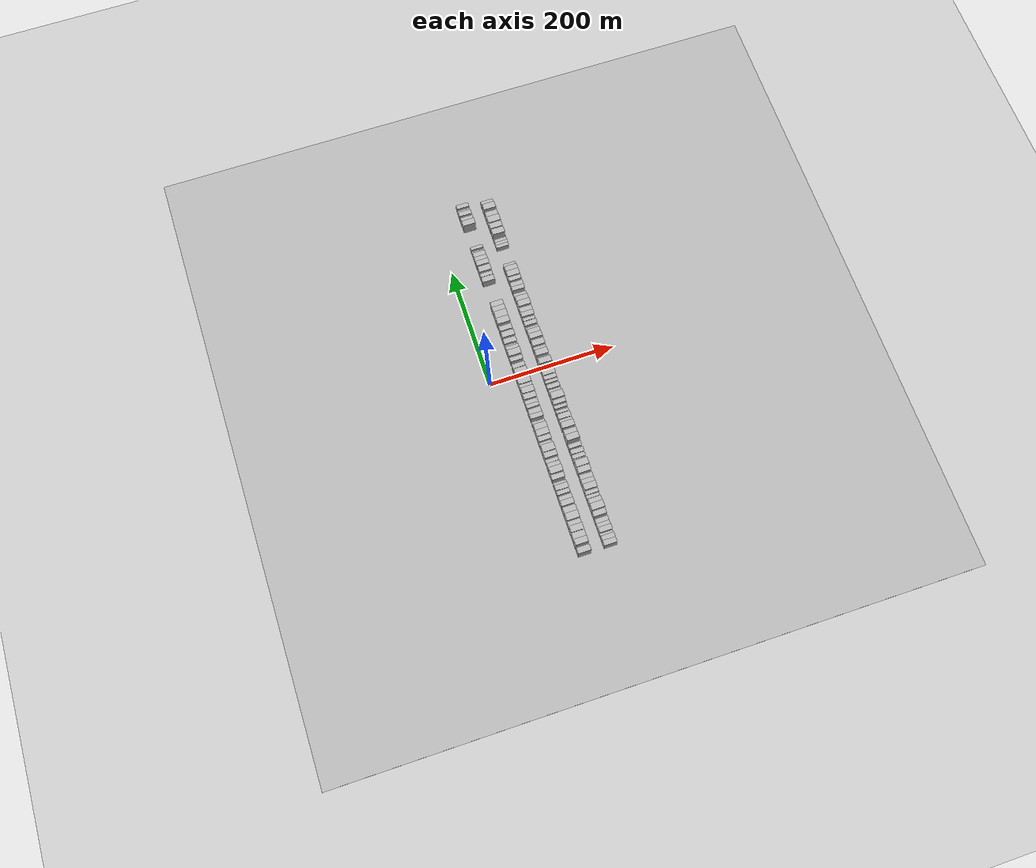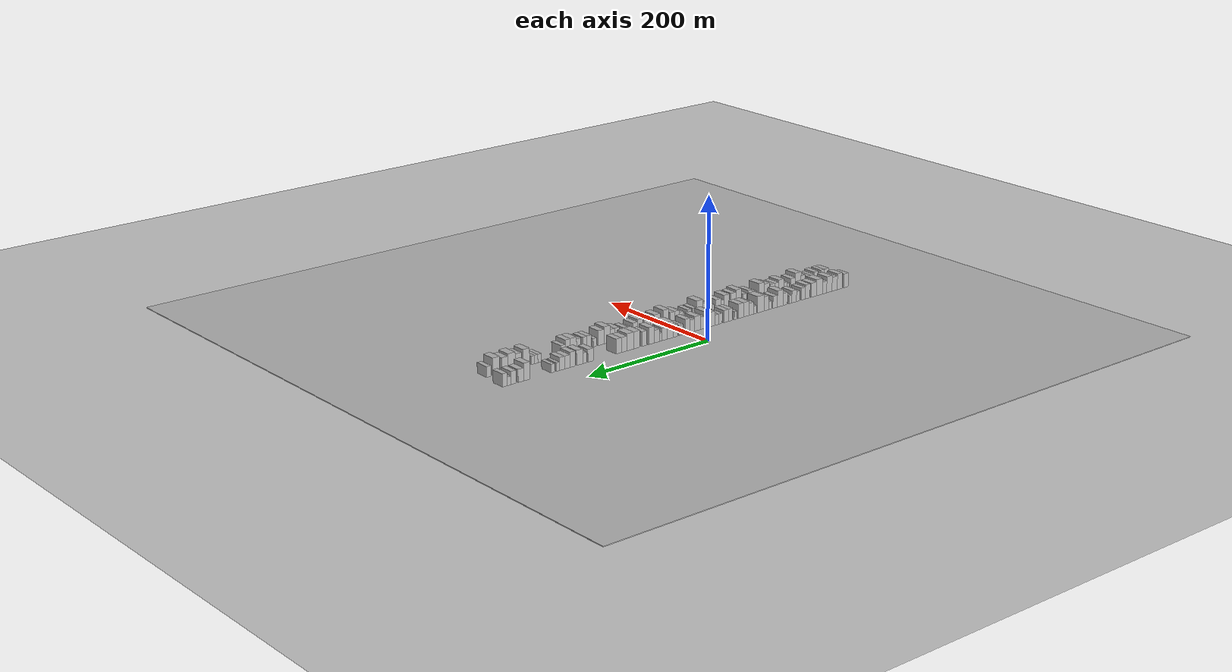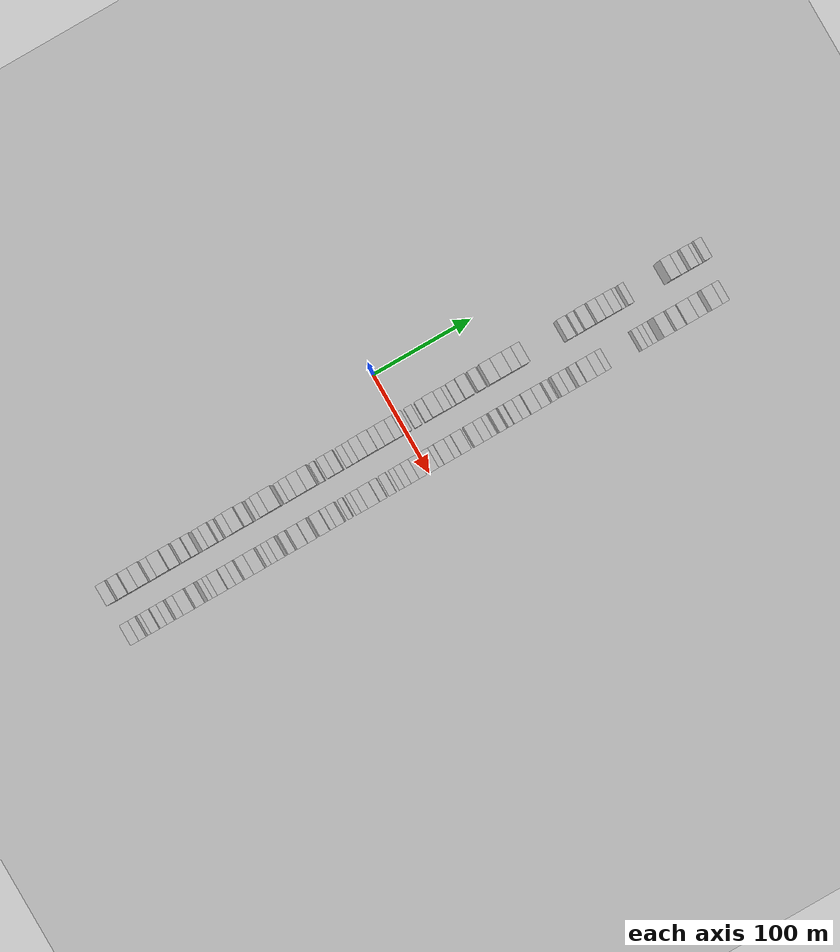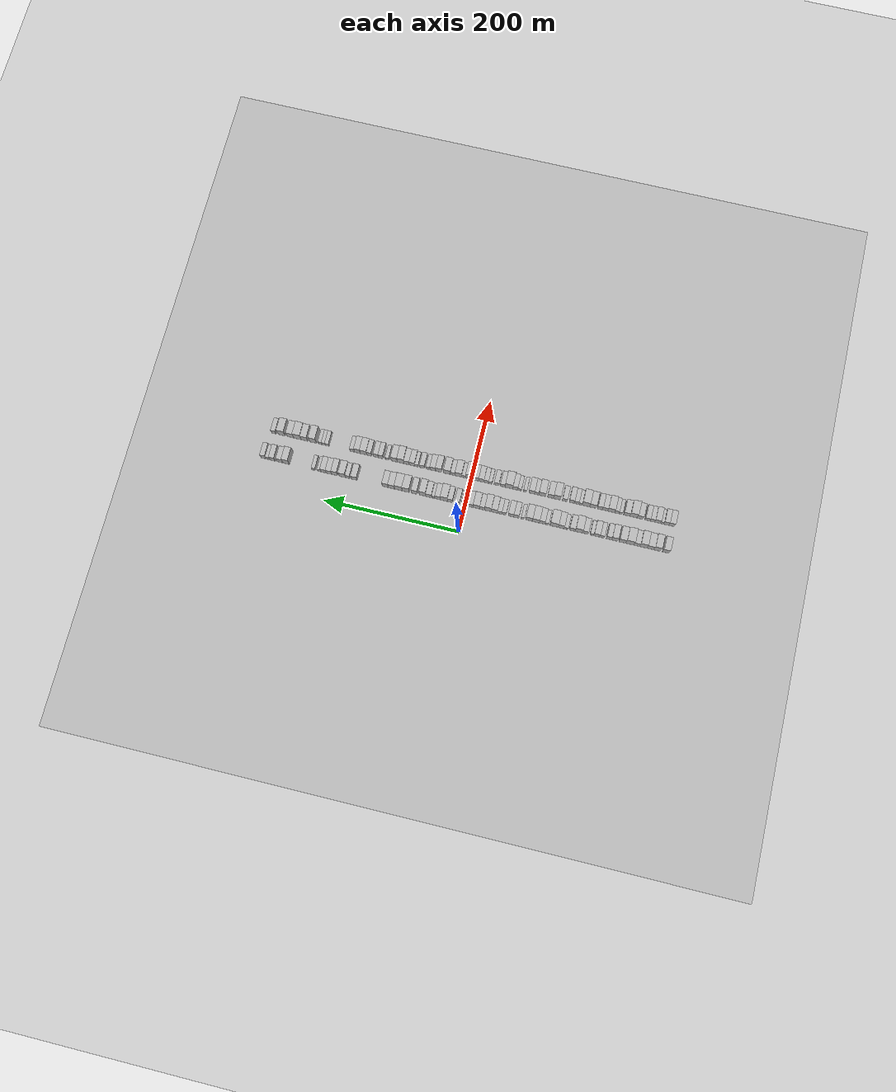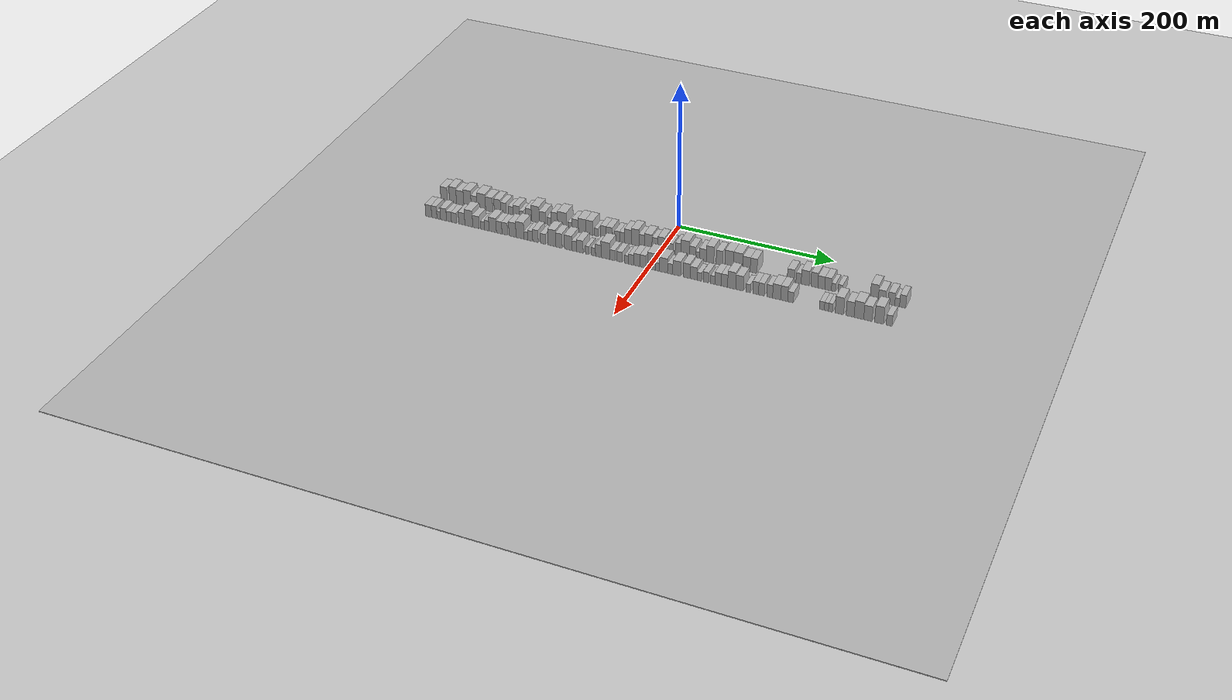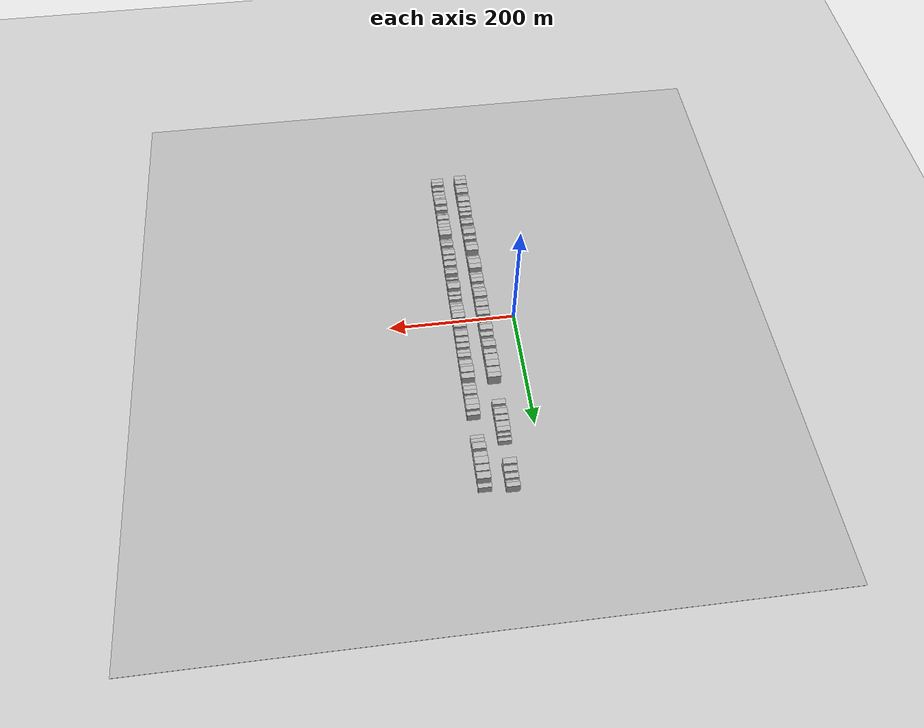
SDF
<?xml version="1.0" encoding="utf-8"?>

<sdf version="1.6">

   <world name="default">

      <gui fullscreen="0">

         <camera name="user_camera">

            <pose>-15 0 4.57585 0 0 0</pose>

            <view_controller>orbit</view_controller>

         </camera>

      </gui>

      <scene>

         <sky>

           <clouds>

             <speed>12</speed>

           </clouds>

         </sky>

         <ambient>0.4 0.4 0.4 1</ambient>

         <background>0.7 0.7 0.7 1</background>

         <shadows>1</shadows>

      </scene>

      <gravity>0 0 -9.8066</gravity>

      <magnetic_field>6e-06 2.3e-05 -4.2e-05</magnetic_field>

      <physics default="0" name="default_physics" type="ode">

         <ode>

            <solver>

               <type>quick</type>

               <iters>10</iters>

               <sor>1.0</sor>

               <use_dynamic_moi_rescaling>0</use_dynamic_moi_rescaling>

            </solver>

            <constraints>

               <cfm>0</cfm>

               <erp>0.2</erp>

               <contact_max_correcting_vel>100</contact_max_correcting_vel>

               <contact_surface_layer>0.001</contact_surface_layer>

            </constraints>

         </ode>

         <max_step_size>0.004</max_step_size>

         <real_time_factor>1</real_time_factor>

         <real_time_update_rate>250</real_time_update_rate>

      </physics>

      <light name="sun" type="directional">

         <cast_shadows>1</cast_shadows>

         <pose>0 0 10 0 0 0</pose>

         <diffuse>0.8 0.8 0.8 1</diffuse>

         <specular>0.2 0.2 0.2 1</specular>

         <attenuation>

            <range>1000</range>

            <constant>0.9</constant>

            <linear>0.01</linear>

            <quadratic>0.001</quadratic>

         </attenuation>

         <direction>-0.5 0.1 -0.9</direction>

      </light>

      <include>

         <name>ground_plane_1</name>

         <uri>model://HANNAS_ground_plane</uri>

         <pose>0 0 0  0 0 0</pose>

      </include>

      <include>

         <name>ground_plane_2</name>

         <uri>model://HANNAS_ground_plane</uri>

         <pose>100 0 0  0 0 0</pose>

      </include>

      <model name="building_1">

         <static>1</static>

         <pose frame="">50.0000 -295.3019 0 0.000000 0.000000 0.000000</pose>

         <link name="link">

            <pose frame="">0 0 10.50 0 0 0</pose>

            <collision name="collision">

               <geometry>

                  <box>

                     <size>20.0000 9.3963 21.0000</size>

                  </box>

               </geometry>

               <max_contacts>10</max_contacts>

               <surface>

                  <contact>

                     <ode/>

                  </contact>

                  <bounce/>

                  <friction>

                     <torsional>

                        <ode/>

                     </torsional>

                     <ode/>

                  </friction>

               </surface>

            </collision>

            <visual name="visual">

               <cast_shadows>0</cast_shadows>

               <geometry>

                  <box>

                     <size>20.0000 9.3963 21.0000</size>

                  </box>

               </geometry>

               <material>

                  <script>

                     <uri>model://HANNAS_wall/materials/scripts</uri>

                     <uri>model://HANNAS_wall/materials/textures</uri>

                     <name>vrc/HANNAS_wall</name>

                  </script>

               </material>

            </visual>

            <self_collide>0</self_collide>

            <enable_wind>0</enable_wind>

            <kinematic>0</kinematic>

         </link>

      </model>

      <model name="building_2">

         <static>1</static>

         <pose frame="">50.0000 -282.7249 0 0.000000 0.000000 0.000000</pose>

         <link name="link">

            <pose frame="">0 0 12.00 0 0 0</pose>

            <collision name="collision">

               <geometry>

                  <box>

                     <size>20.0000 9.7576 24.0000</size>

                  </box>

               </geometry>

               <max_contacts>10</max_contacts>

               <surface>

                  <contact>

                     <ode/>

                  </contact>

                  <bounce/>

                  <friction>

                     <torsional>

                        <ode/>

                     </torsional>

                     <ode/>

                  </friction>

               </surface>

            </collision>

            <visual name="visual">

               <cast_shadows>0</cast_shadows>

               <geometry>

                  <box>

                     <size>20.0000 9.7576 24.0000</size>

                  </box>

               </geometry>

               <material>

                  <script>

                     <uri>model://HANNAS_wall/materials/scripts</uri>

                     <uri>model://HANNAS_wall/materials/textures</uri>

                     <name>vrc/HANNAS_wall</name>

                  </script>

               </material>

            </visual>

            <self_collide>0</self_collide>

            <enable_wind>0</enable_wind>

            <kinematic>0</kinematic>

         </link>

      </model>

      <model name="building_3">

         <static>1</static>

         <pose frame="">50.0000 -272.7034 0 0.000000 0.000000 0.000000</pose>

         <link name="link">

            <pose frame="">0 0 10.50 0 0 0</pose>

            <collision name="collision">

               <geometry>

                  <box>

                     <size>20.0000 10.2854 21.0000</size>

                  </box>

               </geometry>

               <max_contacts>10</max_contacts>

               <surface>

                  <contact>

                     <ode/>

                  </contact>

                  <bounce/>

                  <friction>

                     <torsional>

                        <ode/>

                     </torsional>

                     <ode/>

                  </friction>

               </surface>

            </collision>

            <visual name="visual">

               <cast_shadows>0</cast_shadows>

               <geometry>

                  <box>

                     <size>20.0000 10.2854 21.0000</size>

                  </box>

               </geometry>

               <material>

                  <script>

                     <uri>model://HANNAS_wall/materials/scripts</uri>

                     <uri>model://HANNAS_wall/materials/textures</uri>

                     <name>vrc/HANNAS_wall</name>

                  </script>

               </material>

            </visual>

            <self_collide>0</self_collide>

            <enable_wind>0</enable_wind>

            <kinematic>0</kinematic>

         </link>

      </model>

      <model name="building_4">

         <static>1</static>

         <pose frame="">50.0000 -262.3470 0 0.000000 0.000000 0.000000</pose>

         <link name="link">

            <pose frame="">0 0 12.00 0 0 0</pose>

            <collision name="collision">

               <geometry>

                  <box>

                     <size>20.0000 10.4274 24.0000</size>

                  </box>

               </geometry>

               <max_contacts>10</max_contacts>

               <surface>

                  <contact>

                     <ode/>

                  </contact>

                  <bounce/>

                  <friction>

                     <torsional>

                        <ode/>

                     </torsional>

                     <ode/>

                  </friction>

               </surface>

            </collision>

            <visual name="visual">

               <cast_shadows>0</cast_shadows>

               <geometry>

                  <box>

                     <size>20.0000 10.4274 24.0000</size>

                  </box>

               </geometry>

               <material>

                  <script>

                     <uri>model://HANNAS_wall/materials/scripts</uri>

                     <uri>model://HANNAS_wall/materials/textures</uri>

                     <name>vrc/HANNAS_wall</name>

                  </script>

               </material>

            </visual>

            <self_collide>0</self_collide>

            <enable_wind>0</enable_wind>

            <kinematic>0</kinematic>

         </link>

      </model>

      <model name="building_5">

         <static>1</static>

         <pose frame="">50.0000 -252.9480 0 0.000000 0.000000 0.000000</pose>

         <link name="link">

            <pose frame="">0 0 9.00 0 0 0</pose>

            <collision name="collision">

               <geometry>

                  <box>

                     <size>20.0000 8.3706 18.0000</size>

                  </box>

               </geometry>

               <max_contacts>10</max_contacts>

               <surface>

                  <contact>

                     <ode/>

                  </contact>

                  <bounce/>

                  <friction>

                     <torsional>

                        <ode/>

                     </torsional>

                     <ode/>

                  </friction>

               </surface>

            </collision>

            <visual name="visual">

               <cast_shadows>0</cast_shadows>

               <geometry>

                  <box>

                     <size>20.0000 8.3706 18.0000</size>

                  </box>

               </geometry>

               <material>

                  <script>

                     <uri>model://HANNAS_wall/materials/scripts</uri>

                     <uri>model://HANNAS_wall/materials/textures</uri>

                     <name>vrc/HANNAS_wall</name>

                  </script>

               </material>

            </visual>

            <self_collide>0</self_collide>

            <enable_wind>0</enable_wind>

            <kinematic>0</kinematic>

         </link>

      </model>

      <model name="building_6">

         <static>1</static>

         <pose frame="">50.0000 -242.8675 0 0.000000 0.000000 0.000000</pose>

         <link name="link">

            <pose frame="">0 0 12.00 0 0 0</pose>

            <collision name="collision">

               <geometry>

                  <box>

                     <size>20.0000 11.7904 24.0000</size>

                  </box>

               </geometry>

               <max_contacts>10</max_contacts>

               <surface>

                  <contact>

                     <ode/>

                  </contact>

                  <bounce/>

                  <friction>

                     <torsional>

                        <ode/>

                     </torsional>

                     <ode/>

                  </friction>

               </surface>

            </collision>

            <visual name="visual">

               <cast_shadows>0</cast_shadows>

               <geometry>

                  <box>

                     <size>20.0000 11.7904 24.0000</size>

                  </box>

               </geometry>

               <material>

                  <script>

                     <uri>model://HANNAS_wall/materials/scripts</uri>

                     <uri>model://HANNAS_wall/materials/textures</uri>

                     <name>vrc/HANNAS_wall</name>

                  </script>

               </material>

            </visual>

            <self_collide>0</self_collide>

            <enable_wind>0</enable_wind>

            <kinematic>0</kinematic>

         </link>

      </model>

      <model name="building_7">

         <static>1</static>

         <pose frame="">50.0000 -231.9022 0 0.000000 0.000000 0.000000</pose>

         <link name="link">

            <pose frame="">0 0 10.50 0 0 0</pose>

            <collision name="collision">

               <geometry>

                  <box>

                     <size>20.0000 10.1402 21.0000</size>

                  </box>

               </geometry>

               <max_contacts>10</max_contacts>

               <surface>

                  <contact>

                     <ode/>

                  </contact>

                  <bounce/>

                  <friction>

                     <torsional>

                        <ode/>

                     </torsional>

                     <ode/>

                  </friction>

               </surface>

            </collision>

            <visual name="visual">

               <cast_shadows>0</cast_shadows>

               <geometry>

                  <box>

                     <size>20.0000 10.1402 21.0000</size>

                  </box>

               </geometry>

               <material>

                  <script>

                     <uri>model://HANNAS_wall/materials/scripts</uri>

                     <uri>model://HANNAS_wall/materials/textures</uri>

                     <name>vrc/HANNAS_wall</name>

                  </script>

               </material>

            </visual>

            <self_collide>0</self_collide>

            <enable_wind>0</enable_wind>

            <kinematic>0</kinematic>

         </link>

      </model>

      <model name="building_8">

         <static>1</static>

         <pose frame="">50.0000 -220.3504 0 0.000000 0.000000 0.000000</pose>

         <link name="link">

            <pose frame="">0 0 10.50 0 0 0</pose>

            <collision name="collision">

               <geometry>

                  <box>

                     <size>20.0000 8.9634 21.0000</size>

                  </box>

               </geometry>

               <max_contacts>10</max_contacts>

               <surface>

                  <contact>

                     <ode/>

                  </contact>

                  <bounce/>

                  <friction>

                     <torsional>

                        <ode/>

                     </torsional>

                     <ode/>

                  </friction>

               </surface>

            </collision>

            <visual name="visual">

               <cast_shadows>0</cast_shadows>

               <geometry>

                  <box>

                     <size>20.0000 8.9634 21.0000</size>

                  </box>

               </geometry>

               <material>

                  <script>

                     <uri>model://HANNAS_wall/materials/scripts</uri>

                     <uri>model://HANNAS_wall/materials/textures</uri>

                     <name>vrc/HANNAS_wall</name>

                  </script>

               </material>

            </visual>

            <self_collide>0</self_collide>

            <enable_wind>0</enable_wind>

            <kinematic>0</kinematic>

         </link>

      </model>

      <model name="building_9">

         <static>1</static>

         <pose frame="">50.0000 -212.1136 0 0.000000 0.000000 0.000000</pose>

         <link name="link">

            <pose frame="">0 0 9.00 0 0 0</pose>

            <collision name="collision">

               <geometry>

                  <box>

                     <size>20.0000 7.5102 18.0000</size>

                  </box>

               </geometry>

               <max_contacts>10</max_contacts>

               <surface>

                  <contact>

                     <ode/>

                  </contact>

                  <bounce/>

                  <friction>

                     <torsional>

                        <ode/>

                     </torsional>

                     <ode/>

                  </friction>

               </surface>

            </collision>

            <visual name="visual">

               <cast_shadows>0</cast_shadows>

               <geometry>

                  <box>

                     <size>20.0000 7.5102 18.0000</size>

                  </box>

               </geometry>

               <material>

                  <script>

                     <uri>model://HANNAS_wall/materials/scripts</uri>

                     <uri>model://HANNAS_wall/materials/textures</uri>

                     <name>vrc/HANNAS_wall</name>

                  </script>

               </material>

            </visual>

            <self_collide>0</self_collide>

            <enable_wind>0</enable_wind>

            <kinematic>0</kinematic>

         </link>

      </model>

      <model name="building_10">

         <static>1</static>

         <pose frame="">50.0000 -202.0355 0 0.000000 0.000000 0.000000</pose>

         <link name="link">

            <pose frame="">0 0 7.50 0 0 0</pose>

            <collision name="collision">

               <geometry>

                  <box>

                     <size>20.0000 6.6459 15.0000</size>

                  </box>

               </geometry>

               <max_contacts>10</max_contacts>

               <surface>

                  <contact>

                     <ode/>

                  </contact>

                  <bounce/>

                  <friction>

                     <torsional>

                        <ode/>

                     </torsional>

                     <ode/>

                  </friction>

               </surface>

            </collision>

            <visual name="visual">

               <cast_shadows>0</cast_shadows>

               <geometry>

                  <box>

                     <size>20.0000 6.6459 15.0000</size>

                  </box>

               </geometry>

               <material>

                  <script>

                     <uri>model://HANNAS_wall/materials/scripts</uri>

                     <uri>model://HANNAS_wall/materials/textures</uri>

                     <name>vrc/HANNAS_wall</name>

                  </script>

               </material>

            </visual>

            <self_collide>0</self_collide>

            <enable_wind>0</enable_wind>

            <kinematic>0</kinematic>

         </link>

      </model>

      <model name="building_11">

         <static>1</static>

         <pose frame="">50.0000 -194.3298 0 0.000000 0.000000 0.000000</pose>

         <link name="link">

            <pose frame="">0 0 9.00 0 0 0</pose>

            <collision name="collision">

               <geometry>

                  <box>

                     <size>20.0000 8.7655 18.0000</size>

                  </box>

               </geometry>

               <max_contacts>10</max_contacts>

               <surface>

                  <contact>

                     <ode/>

                  </contact>

                  <bounce/>

                  <friction>

                     <torsional>

                        <ode/>

                     </torsional>

                     <ode/>

                  </friction>

               </surface>

            </collision>

            <visual name="visual">

               <cast_shadows>0</cast_shadows>

               <geometry>

                  <box>

                     <size>20.0000 8.7655 18.0000</size>

                  </box>

               </geometry>

               <material>

                  <script>

                     <uri>model://HANNAS_wall/materials/scripts</uri>

                     <uri>model://HANNAS_wall/materials/textures</uri>

                     <name>vrc/HANNAS_wall</name>

                  </script>

               </material>

            </visual>

            <self_collide>0</self_collide>

            <enable_wind>0</enable_wind>

            <kinematic>0</kinematic>

         </link>

      </model>

      <model name="building_12">

         <static>1</static>

         <pose frame="">50.0000 -187.2509 0 0.000000 0.000000 0.000000</pose>

         <link name="link">

            <pose frame="">0 0 6.00 0 0 0</pose>

            <collision name="collision">

               <geometry>

                  <box>

                     <size>20.0000 5.3923 12.0000</size>

                  </box>

               </geometry>

               <max_contacts>10</max_contacts>

               <surface>

                  <contact>

                     <ode/>

                  </contact>

                  <bounce/>

                  <friction>

                     <torsional>

                        <ode/>

                     </torsional>

                     <ode/>

                  </friction>

               </surface>

            </collision>

            <visual name="visual">

               <cast_shadows>0</cast_shadows>

               <geometry>

                  <box>

                     <size>20.0000 5.3923 12.0000</size>

                  </box>

               </geometry>

               <material>

                  <script>

                     <uri>model://HANNAS_wall/materials/scripts</uri>

                     <uri>model://HANNAS_wall/materials/textures</uri>

                     <name>vrc/HANNAS_wall</name>

                  </script>

               </material>

            </visual>

            <self_collide>0</self_collide>

            <enable_wind>0</enable_wind>

            <kinematic>0</kinematic>

         </link>

      </model>

      <model name="building_13">

         <static>1</static>

         <pose frame="">50.0000 -177.4368 0 0.000000 0.000000 0.000000</pose>

         <link name="link">

            <pose frame="">0 0 9.00 0 0 0</pose>

            <collision name="collision">

               <geometry>

                  <box>

                     <size>20.0000 8.2360 18.0000</size>

                  </box>

               </geometry>

               <max_contacts>10</max_contacts>

               <surface>

                  <contact>

                     <ode/>

                  </contact>

                  <bounce/>

                  <friction>

                     <torsional>

                        <ode/>

                     </torsional>

                     <ode/>

                  </friction>

               </surface>

            </collision>

            <visual name="visual">

               <cast_shadows>0</cast_shadows>

               <geometry>

                  <box>

                     <size>20.0000 8.2360 18.0000</size>

                  </box>

               </geometry>

               <material>

                  <script>

                     <uri>model://HANNAS_wall/materials/scripts</uri>

                     <uri>model://HANNAS_wall/materials/textures</uri>

                     <name>vrc/HANNAS_wall</name>

                  </script>

               </material>

            </visual>

            <self_collide>0</self_collide>

            <enable_wind>0</enable_wind>

            <kinematic>0</kinematic>

         </link>

      </model>

      <model name="building_14">

         <static>1</static>

         <pose frame="">50.0000 -167.9649 0 0.000000 0.000000 0.000000</pose>

         <link name="link">

            <pose frame="">0 0 12.00 0 0 0</pose>

            <collision name="collision">

               <geometry>

                  <box>

                     <size>20.0000 10.7077 24.0000</size>

                  </box>

               </geometry>

               <max_contacts>10</max_contacts>

               <surface>

                  <contact>

                     <ode/>

                  </contact>

                  <bounce/>

                  <friction>

                     <torsional>

                        <ode/>

                     </torsional>

                     <ode/>

                  </friction>

               </surface>

            </collision>

            <visual name="visual">

               <cast_shadows>0</cast_shadows>

               <geometry>

                  <box>

                     <size>20.0000 10.7077 24.0000</size>

                  </box>

               </geometry>

               <material>

                  <script>

                     <uri>model://HANNAS_wall/materials/scripts</uri>

                     <uri>model://HANNAS_wall/materials/textures</uri>

                     <name>vrc/HANNAS_wall</name>

                  </script>

               </material>

            </visual>

            <self_collide>0</self_collide>

            <enable_wind>0</enable_wind>

            <kinematic>0</kinematic>

         </link>

      </model>

      <model name="building_15">

         <static>1</static>

         <pose frame="">50.0000 -158.4264 0 0.000000 0.000000 0.000000</pose>

         <link name="link">

            <pose frame="">0 0 9.00 0 0 0</pose>

            <collision name="collision">

               <geometry>

                  <box>

                     <size>20.0000 8.3694 18.0000</size>

                  </box>

               </geometry>

               <max_contacts>10</max_contacts>

               <surface>

                  <contact>

                     <ode/>

                  </contact>

                  <bounce/>

                  <friction>

                     <torsional>

                        <ode/>

                     </torsional>

                     <ode/>

                  </friction>

               </surface>

            </collision>

            <visual name="visual">

               <cast_shadows>0</cast_shadows>

               <geometry>

                  <box>

                     <size>20.0000 8.3694 18.0000</size>

                  </box>

               </geometry>

               <material>

                  <script>

                     <uri>model://HANNAS_wall/materials/scripts</uri>

                     <uri>model://HANNAS_wall/materials/textures</uri>

                     <name>vrc/HANNAS_wall</name>

                  </script>

               </material>

            </visual>

            <self_collide>0</self_collide>

            <enable_wind>0</enable_wind>

            <kinematic>0</kinematic>

         </link>

      </model>

      <model name="building_16">

         <static>1</static>

         <pose frame="">50.0000 -149.3047 0 0.000000 0.000000 0.000000</pose>

         <link name="link">

            <pose frame="">0 0 6.00 0 0 0</pose>

            <collision name="collision">

               <geometry>

                  <box>

                     <size>20.0000 5.8741 12.0000</size>

                  </box>

               </geometry>

               <max_contacts>10</max_contacts>

               <surface>

                  <contact>

                     <ode/>

                  </contact>

                  <bounce/>

                  <friction>

                     <torsional>

                        <ode/>

                     </torsional>

                     <ode/>

                  </friction>

               </surface>

            </collision>

            <visual name="visual">

               <cast_shadows>0</cast_shadows>

               <geometry>

                  <box>

                     <size>20.0000 5.8741 12.0000</size>

                  </box>

               </geometry>

               <material>

                  <script>

                     <uri>model://HANNAS_wall/materials/scripts</uri>

                     <uri>model://HANNAS_wall/materials/textures</uri>

                     <name>vrc/HANNAS_wall</name>

                  </script>

               </material>

            </visual>

            <self_collide>0</self_collide>

            <enable_wind>0</enable_wind>

            <kinematic>0</kinematic>

         </link>

      </model>

      <model name="building_17">

         <static>1</static>

         <pose frame="">50.0000 -141.9949 0 0.000000 0.000000 0.000000</pose>

         <link name="link">

            <pose frame="">0 0 10.50 0 0 0</pose>

            <collision name="collision">

               <geometry>

                  <box>

                     <size>20.0000 8.7454 21.0000</size>

                  </box>

               </geometry>

               <max_contacts>10</max_contacts>

               <surface>

                  <contact>

                     <ode/>

                  </contact>

                  <bounce/>

                  <friction>

                     <torsional>

                        <ode/>

                     </torsional>

                     <ode/>

                  </friction>

               </surface>

            </collision>

            <visual name="visual">

               <cast_shadows>0</cast_shadows>

               <geometry>

                  <box>

                     <size>20.0000 8.7454 21.0000</size>

                  </box>

               </geometry>

               <material>

                  <script>

                     <uri>model://HANNAS_wall/materials/scripts</uri>

                     <uri>model://HANNAS_wall/materials/textures</uri>

                     <name>vrc/HANNAS_wall</name>

                  </script>

               </material>

            </visual>

            <self_collide>0</self_collide>

            <enable_wind>0</enable_wind>

            <kinematic>0</kinematic>

         </link>

      </model>

      <model name="building_18">

         <static>1</static>

         <pose frame="">50.0000 -131.6551 0 0.000000 0.000000 0.000000</pose>

         <link name="link">

            <pose frame="">0 0 12.00 0 0 0</pose>

            <collision name="collision">

               <geometry>

                  <box>

                     <size>20.0000 11.9344 24.0000</size>

                  </box>

               </geometry>

               <max_contacts>10</max_contacts>

               <surface>

                  <contact>

                     <ode/>

                  </contact>

                  <bounce/>

                  <friction>

                     <torsional>

                        <ode/>

                     </torsional>

                     <ode/>

                  </friction>

               </surface>

            </collision>

            <visual name="visual">

               <cast_shadows>0</cast_shadows>

               <geometry>

                  <box>

                     <size>20.0000 11.9344 24.0000</size>

                  </box>

               </geometry>

               <material>

                  <script>

                     <uri>model://HANNAS_wall/materials/scripts</uri>

                     <uri>model://HANNAS_wall/materials/textures</uri>

                     <name>vrc/HANNAS_wall</name>

                  </script>

               </material>

            </visual>

            <self_collide>0</self_collide>

            <enable_wind>0</enable_wind>

            <kinematic>0</kinematic>

         </link>

      </model>

      <model name="building_19">

         <static>1</static>

         <pose frame="">50.0000 -120.9007 0 0.000000 0.000000 0.000000</pose>

         <link name="link">

            <pose frame="">0 0 6.00 0 0 0</pose>

            <collision name="collision">

               <geometry>

                  <box>

                     <size>20.0000 5.5743 12.0000</size>

                  </box>

               </geometry>

               <max_contacts>10</max_contacts>

               <surface>

                  <contact>

                     <ode/>

                  </contact>

                  <bounce/>

                  <friction>

                     <torsional>

                        <ode/>

                     </torsional>

                     <ode/>

                  </friction>

               </surface>

            </collision>

            <visual name="visual">

               <cast_shadows>0</cast_shadows>

               <geometry>

                  <box>

                     <size>20.0000 5.5743 12.0000</size>

                  </box>

               </geometry>

               <material>

                  <script>

                     <uri>model://HANNAS_wall/materials/scripts</uri>

                     <uri>model://HANNAS_wall/materials/textures</uri>

                     <name>vrc/HANNAS_wall</name>

                  </script>

               </material>

            </visual>

            <self_collide>0</self_collide>

            <enable_wind>0</enable_wind>

            <kinematic>0</kinematic>

         </link>

      </model>

      <model name="building_20">

         <static>1</static>

         <pose frame="">50.0000 -114.0491 0 0.000000 0.000000 0.000000</pose>

         <link name="link">

            <pose frame="">0 0 9.00 0 0 0</pose>

            <collision name="collision">

               <geometry>

                  <box>

                     <size>20.0000 8.1289 18.0000</size>

                  </box>

               </geometry>

               <max_contacts>10</max_contacts>

               <surface>

                  <contact>

                     <ode/>

                  </contact>

                  <bounce/>

                  <friction>

                     <torsional>

                        <ode/>

                     </torsional>

                     <ode/>

                  </friction>

               </surface>

            </collision>

            <visual name="visual">

               <cast_shadows>0</cast_shadows>

               <geometry>

                  <box>

                     <size>20.0000 8.1289 18.0000</size>

                  </box>

               </geometry>

               <material>

                  <script>

                     <uri>model://HANNAS_wall/materials/scripts</uri>

                     <uri>model://HANNAS_wall/materials/textures</uri>

                     <name>vrc/HANNAS_wall</name>

                  </script>

               </material>

            </visual>

            <self_collide>0</self_collide>

            <enable_wind>0</enable_wind>

            <kinematic>0</kinematic>

         </link>

      </model>

      <model name="building_21">

         <static>1</static>

         <pose frame="">50.0000 -104.8026 0 0.000000 0.000000 0.000000</pose>

         <link name="link">

            <pose frame="">0 0 10.50 0 0 0</pose>

            <collision name="collision">

               <geometry>

                  <box>

                     <size>20.0000 10.3641 21.0000</size>

                  </box>

               </geometry>

               <max_contacts>10</max_contacts>

               <surface>

                  <contact>

                     <ode/>

                  </contact>

                  <bounce/>

                  <friction>

                     <torsional>

                        <ode/>

                     </torsional>

                     <ode/>

                  </friction>

               </surface>

            </collision>

            <visual name="visual">

               <cast_shadows>0</cast_shadows>

               <geometry>

                  <box>

                     <size>20.0000 10.3641 21.0000</size>

                  </box>

               </geometry>

               <material>

                  <script>

                     <uri>model://HANNAS_wall/materials/scripts</uri>

                     <uri>model://HANNAS_wall/materials/textures</uri>

                     <name>vrc/HANNAS_wall</name>

                  </script>

               </material>

            </visual>

            <self_collide>0</self_collide>

            <enable_wind>0</enable_wind>

            <kinematic>0</kinematic>

         </link>

      </model>

      <model name="building_22">

         <static>1</static>

         <pose frame="">50.0000 -94.7582 0 0.000000 0.000000 0.000000</pose>

         <link name="link">

            <pose frame="">0 0 10.50 0 0 0</pose>

            <collision name="collision">

               <geometry>

                  <box>

                     <size>20.0000 9.7247 21.0000</size>

                  </box>

               </geometry>

               <max_contacts>10</max_contacts>

               <surface>

                  <contact>

                     <ode/>

                  </contact>

                  <bounce/>

                  <friction>

                     <torsional>

                        <ode/>

                     </torsional>

                     <ode/>

                  </friction>

               </surface>

            </collision>

            <visual name="visual">

               <cast_shadows>0</cast_shadows>

               <geometry>

                  <box>

                     <size>20.0000 9.7247 21.0000</size>

                  </box>

               </geometry>

               <material>

                  <script>

                     <uri>model://HANNAS_wall/materials/scripts</uri>

                     <uri>model://HANNAS_wall/materials/textures</uri>

                     <name>vrc/HANNAS_wall</name>

                  </script>

               </material>

            </visual>

            <self_collide>0</self_collide>

            <enable_wind>0</enable_wind>

            <kinematic>0</kinematic>

         </link>

      </model>

      <model name="building_23">

         <static>1</static>

         <pose frame="">50.0000 -85.3708 0 0.000000 0.000000 0.000000</pose>

         <link name="link">

            <pose frame="">0 0 6.00 0 0 0</pose>

            <collision name="collision">

               <geometry>

                  <box>

                     <size>20.0000 5.0501 12.0000</size>

                  </box>

               </geometry>

               <max_contacts>10</max_contacts>

               <surface>

                  <contact>

                     <ode/>

                  </contact>

                  <bounce/>

                  <friction>

                     <torsional>

                        <ode/>

                     </torsional>

                     <ode/>

                  </friction>

               </surface>

            </collision>

            <visual name="visual">

               <cast_shadows>0</cast_shadows>

               <geometry>

                  <box>

                     <size>20.0000 5.0501 12.0000</size>

                  </box>

               </geometry>

               <material>

                  <script>

                     <uri>model://HANNAS_wall/materials/scripts</uri>

                     <uri>model://HANNAS_wall/materials/textures</uri>

                     <name>vrc/HANNAS_wall</name>

                  </script>

               </material>

            </visual>

            <self_collide>0</self_collide>

            <enable_wind>0</enable_wind>

            <kinematic>0</kinematic>

         </link>

      </model>

      <model name="building_24">

         <static>1</static>

         <pose frame="">50.0000 -76.0046 0 0.000000 0.000000 0.000000</pose>

         <link name="link">

            <pose frame="">0 0 9.00 0 0 0</pose>

            <collision name="collision">

               <geometry>

                  <box>

                     <size>20.0000 7.6823 18.0000</size>

                  </box>

               </geometry>

               <max_contacts>10</max_contacts>

               <surface>

                  <contact>

                     <ode/>

                  </contact>

                  <bounce/>

                  <friction>

                     <torsional>

                        <ode/>

                     </torsional>

                     <ode/>

                  </friction>

               </surface>

            </collision>

            <visual name="visual">

               <cast_shadows>0</cast_shadows>

               <geometry>

                  <box>

                     <size>20.0000 7.6823 18.0000</size>

                  </box>

               </geometry>

               <material>

                  <script>

                     <uri>model://HANNAS_wall/materials/scripts</uri>

                     <uri>model://HANNAS_wall/materials/textures</uri>

                     <name>vrc/HANNAS_wall</name>

                  </script>

               </material>

            </visual>

            <self_collide>0</self_collide>

            <enable_wind>0</enable_wind>

            <kinematic>0</kinematic>

         </link>

      </model>

      <model name="building_25">

         <static>1</static>

         <pose frame="">50.0000 -68.0026 0 0.000000 0.000000 0.000000</pose>

         <link name="link">

            <pose frame="">0 0 9.00 0 0 0</pose>

            <collision name="collision">

               <geometry>

                  <box>

                     <size>20.0000 8.3216 18.0000</size>

                  </box>

               </geometry>

               <max_contacts>10</max_contacts>

               <surface>

                  <contact>

                     <ode/>

                  </contact>

                  <bounce/>

                  <friction>

                     <torsional>

                        <ode/>

                     </torsional>

                     <ode/>

                  </friction>

               </surface>

            </collision>

            <visual name="visual">

               <cast_shadows>0</cast_shadows>

               <geometry>

                  <box>

                     <size>20.0000 8.3216 18.0000</size>

                  </box>

               </geometry>

               <material>

                  <script>

                     <uri>model://HANNAS_wall/materials/scripts</uri>

                     <uri>model://HANNAS_wall/materials/textures</uri>

                     <name>vrc/HANNAS_wall</name>

                  </script>

               </material>

            </visual>

            <self_collide>0</self_collide>

            <enable_wind>0</enable_wind>

            <kinematic>0</kinematic>

         </link>

      </model>

      <model name="building_26">

         <static>1</static>

         <pose frame="">50.0000 -57.6527 0 0.000000 0.000000 0.000000</pose>

         <link name="link">

            <pose frame="">0 0 7.50 0 0 0</pose>

            <collision name="collision">

               <geometry>

                  <box>

                     <size>20.0000 6.3781 15.0000</size>

                  </box>

               </geometry>

               <max_contacts>10</max_contacts>

               <surface>

                  <contact>

                     <ode/>

                  </contact>

                  <bounce/>

                  <friction>

                     <torsional>

                        <ode/>

                     </torsional>

                     <ode/>

                  </friction>

               </surface>

            </collision>

            <visual name="visual">

               <cast_shadows>0</cast_shadows>

               <geometry>

                  <box>

                     <size>20.0000 6.3781 15.0000</size>

                  </box>

               </geometry>

               <material>

                  <script>

                     <uri>model://HANNAS_wall/materials/scripts</uri>

                     <uri>model://HANNAS_wall/materials/textures</uri>

                     <name>vrc/HANNAS_wall</name>

                  </script>

               </material>

            </visual>

            <self_collide>0</self_collide>

            <enable_wind>0</enable_wind>

            <kinematic>0</kinematic>

         </link>

      </model>

      <model name="building_27">

         <static>1</static>

         <pose frame="">50.0000 -51.2100 0 0.000000 0.000000 0.000000</pose>

         <link name="link">

            <pose frame="">0 0 7.50 0 0 0</pose>

            <collision name="collision">

               <geometry>

                  <box>

                     <size>20.0000 6.5072 15.0000</size>

                  </box>

               </geometry>

               <max_contacts>10</max_contacts>

               <surface>

                  <contact>

                     <ode/>

                  </contact>

                  <bounce/>

                  <friction>

                     <torsional>

                        <ode/>

                     </torsional>

                     <ode/>

                  </friction>

               </surface>

            </collision>

            <visual name="visual">

               <cast_shadows>0</cast_shadows>

               <geometry>

                  <box>

                     <size>20.0000 6.5072 15.0000</size>

                  </box>

               </geometry>

               <material>

                  <script>

                     <uri>model://HANNAS_wall/materials/scripts</uri>

                     <uri>model://HANNAS_wall/materials/textures</uri>

                     <name>vrc/HANNAS_wall</name>

                  </script>

               </material>

            </visual>

            <self_collide>0</self_collide>

            <enable_wind>0</enable_wind>

            <kinematic>0</kinematic>

         </link>

      </model>

      <model name="building_28">

         <static>1</static>

         <pose frame="">50.0000 -43.4362 0 0.000000 0.000000 0.000000</pose>

         <link name="link">

            <pose frame="">0 0 10.50 0 0 0</pose>

            <collision name="collision">

               <geometry>

                  <box>

                     <size>20.0000 9.0404 21.0000</size>

                  </box>

               </geometry>

               <max_contacts>10</max_contacts>

               <surface>

                  <contact>

                     <ode/>

                  </contact>

                  <bounce/>

                  <friction>

                     <torsional>

                        <ode/>

                     </torsional>

                     <ode/>

                  </friction>

               </surface>

            </collision>

            <visual name="visual">

               <cast_shadows>0</cast_shadows>

               <geometry>

                  <box>

                     <size>20.0000 9.0404 21.0000</size>

                  </box>

               </geometry>

               <material>

                  <script>

                     <uri>model://HANNAS_wall/materials/scripts</uri>

                     <uri>model://HANNAS_wall/materials/textures</uri>

                     <name>vrc/HANNAS_wall</name>

                  </script>

               </material>

            </visual>

            <self_collide>0</self_collide>

            <enable_wind>0</enable_wind>

            <kinematic>0</kinematic>

         </link>

      </model>

      <model name="building_29">

         <static>1</static>

         <pose frame="">50.0000 -33.9522 0 0.000000 0.000000 0.000000</pose>

         <link name="link">

            <pose frame="">0 0 12.00 0 0 0</pose>

            <collision name="collision">

               <geometry>

                  <box>

                     <size>20.0000 9.9278 24.0000</size>

                  </box>

               </geometry>

               <max_contacts>10</max_contacts>

               <surface>

                  <contact>

                     <ode/>

                  </contact>

                  <bounce/>

                  <friction>

                     <torsional>

                        <ode/>

                     </torsional>

                     <ode/>

                  </friction>

               </surface>

            </collision>

            <visual name="visual">

               <cast_shadows>0</cast_shadows>

               <geometry>

                  <box>

                     <size>20.0000 9.9278 24.0000</size>

                  </box>

               </geometry>

               <material>

                  <script>

                     <uri>model://HANNAS_wall/materials/scripts</uri>

                     <uri>model://HANNAS_wall/materials/textures</uri>

                     <name>vrc/HANNAS_wall</name>

                  </script>

               </material>

            </visual>

            <self_collide>0</self_collide>

            <enable_wind>0</enable_wind>

            <kinematic>0</kinematic>

         </link>

      </model>

      <model name="building_30">

         <static>1</static>

         <pose frame="">50.0000 -25.3044 0 0.000000 0.000000 0.000000</pose>

         <link name="link">

            <pose frame="">0 0 9.00 0 0 0</pose>

            <collision name="collision">

               <geometry>

                  <box>

                     <size>20.0000 7.3676 18.0000</size>

                  </box>

               </geometry>

               <max_contacts>10</max_contacts>

               <surface>

                  <contact>

                     <ode/>

                  </contact>

                  <bounce/>

                  <friction>

                     <torsional>

                        <ode/>

                     </torsional>

                     <ode/>

                  </friction>

               </surface>

            </collision>

            <visual name="visual">

               <cast_shadows>0</cast_shadows>

               <geometry>

                  <box>

                     <size>20.0000 7.3676 18.0000</size>

                  </box>

               </geometry>

               <material>

                  <script>

                     <uri>model://HANNAS_wall/materials/scripts</uri>

                     <uri>model://HANNAS_wall/materials/textures</uri>

                     <name>vrc/HANNAS_wall</name>

                  </script>

               </material>

            </visual>

            <self_collide>0</self_collide>

            <enable_wind>0</enable_wind>

            <kinematic>0</kinematic>

         </link>

      </model>

      <model name="building_31">

         <static>1</static>

         <pose frame="">50.0000 -16.6911 0 0.000000 0.000000 0.000000</pose>

         <link name="link">

            <pose frame="">0 0 10.50 0 0 0</pose>

            <collision name="collision">

               <geometry>

                  <box>

                     <size>20.0000 9.8591 21.0000</size>

                  </box>

               </geometry>

               <max_contacts>10</max_contacts>

               <surface>

                  <contact>

                     <ode/>

                  </contact>

                  <bounce/>

                  <friction>

                     <torsional>

                        <ode/>

                     </torsional>

                     <ode/>

                  </friction>

               </surface>

            </collision>

            <visual name="visual">

               <cast_shadows>0</cast_shadows>

               <geometry>

                  <box>

                     <size>20.0000 9.8591 21.0000</size>

                  </box>

               </geometry>

               <material>

                  <script>

                     <uri>model://HANNAS_wall/materials/scripts</uri>

                     <uri>model://HANNAS_wall/materials/textures</uri>

                     <name>vrc/HANNAS_wall</name>

                  </script>

               </material>

            </visual>

            <self_collide>0</self_collide>

            <enable_wind>0</enable_wind>

            <kinematic>0</kinematic>

         </link>

      </model>

      <model name="building_32">

         <static>1</static>

         <pose frame="">50.0000 -7.8064 0 0.000000 0.000000 0.000000</pose>

         <link name="link">

            <pose frame="">0 0 9.00 0 0 0</pose>

            <collision name="collision">

               <geometry>

                  <box>

                     <size>20.0000 7.9102 18.0000</size>

                  </box>

               </geometry>

               <max_contacts>10</max_contacts>

               <surface>

                  <contact>

                     <ode/>

                  </contact>

                  <bounce/>

                  <friction>

                     <torsional>

                        <ode/>

                     </torsional>

                     <ode/>

                  </friction>

               </surface>

            </collision>

            <visual name="visual">

               <cast_shadows>0</cast_shadows>

               <geometry>

                  <box>

                     <size>20.0000 7.9102 18.0000</size>

                  </box>

               </geometry>

               <material>

                  <script>

                     <uri>model://HANNAS_wall/materials/scripts</uri>

                     <uri>model://HANNAS_wall/materials/textures</uri>

                     <name>vrc/HANNAS_wall</name>

                  </script>

               </material>

            </visual>

            <self_collide>0</self_collide>

            <enable_wind>0</enable_wind>

            <kinematic>0</kinematic>

         </link>

      </model>

      <model name="building_33">

         <static>1</static>

         <pose frame="">50.0000 0.6344 0 0.000000 0.000000 0.000000</pose>

         <link name="link">

            <pose frame="">0 0 10.50 0 0 0</pose>

            <collision name="collision">

               <geometry>

                  <box>

                     <size>20.0000 8.9715 21.0000</size>

                  </box>

               </geometry>

               <max_contacts>10</max_contacts>

               <surface>

                  <contact>

                     <ode/>

                  </contact>

                  <bounce/>

                  <friction>

                     <torsional>

                        <ode/>

                     </torsional>

                     <ode/>

                  </friction>

               </surface>

            </collision>

            <visual name="visual">

               <cast_shadows>0</cast_shadows>

               <geometry>

                  <box>

                     <size>20.0000 8.9715 21.0000</size>

                  </box>

               </geometry>

               <material>

                  <script>

                     <uri>model://HANNAS_wall/materials/scripts</uri>

                     <uri>model://HANNAS_wall/materials/textures</uri>

                     <name>vrc/HANNAS_wall</name>

                  </script>

               </material>

            </visual>

            <self_collide>0</self_collide>

            <enable_wind>0</enable_wind>

            <kinematic>0</kinematic>

         </link>

      </model>

      <model name="building_34">

         <static>1</static>

         <pose frame="">50.0000 11.8369 0 0.000000 0.000000 0.000000</pose>

         <link name="link">

            <pose frame="">0 0 7.50 0 0 0</pose>

            <collision name="collision">

               <geometry>

                  <box>

                     <size>20.0000 7.4334 15.0000</size>

                  </box>

               </geometry>

               <max_contacts>10</max_contacts>

               <surface>

                  <contact>

                     <ode/>

                  </contact>

                  <bounce/>

                  <friction>

                     <torsional>

                        <ode/>

                     </torsional>

                     <ode/>

                  </friction>

               </surface>

            </collision>

            <visual name="visual">

               <cast_shadows>0</cast_shadows>

               <geometry>

                  <box>

                     <size>20.0000 7.4334 15.0000</size>

                  </box>

               </geometry>

               <material>

                  <script>

                     <uri>model://HANNAS_wall/materials/scripts</uri>

                     <uri>model://HANNAS_wall/materials/textures</uri>

                     <name>vrc/HANNAS_wall</name>

                  </script>

               </material>

            </visual>

            <self_collide>0</self_collide>

            <enable_wind>0</enable_wind>

            <kinematic>0</kinematic>

         </link>

      </model>

      <model name="building_35">

         <static>1</static>

         <pose frame="">50.0000 22.2946 0 0.000000 0.000000 0.000000</pose>

         <link name="link">

            <pose frame="">0 0 9.00 0 0 0</pose>

            <collision name="collision">

               <geometry>

                  <box>

                     <size>20.0000 7.4822 18.0000</size>

                  </box>

               </geometry>

               <max_contacts>10</max_contacts>

               <surface>

                  <contact>

                     <ode/>

                  </contact>

                  <bounce/>

                  <friction>

                     <torsional>

                        <ode/>

                     </torsional>

                     <ode/>

                  </friction>

               </surface>

            </collision>

            <visual name="visual">

               <cast_shadows>0</cast_shadows>

               <geometry>

                  <box>

                     <size>20.0000 7.4822 18.0000</size>

                  </box>

               </geometry>

               <material>

                  <script>

                     <uri>model://HANNAS_wall/materials/scripts</uri>

                     <uri>model://HANNAS_wall/materials/textures</uri>

                     <name>vrc/HANNAS_wall</name>

                  </script>

               </material>

            </visual>

            <self_collide>0</self_collide>

            <enable_wind>0</enable_wind>

            <kinematic>0</kinematic>

         </link>

      </model>

      <model name="building_36">

         <static>1</static>

         <pose frame="">50.0000 31.4250 0 0.000000 0.000000 0.000000</pose>

         <link name="link">

            <pose frame="">0 0 12.00 0 0 0</pose>

            <collision name="collision">

               <geometry>

                  <box>

                     <size>20.0000 10.7786 24.0000</size>

                  </box>

               </geometry>

               <max_contacts>10</max_contacts>

               <surface>

                  <contact>

                     <ode/>

                  </contact>

                  <bounce/>

                  <friction>

                     <torsional>

                        <ode/>

                     </torsional>

                     <ode/>

                  </friction>

               </surface>

            </collision>

            <visual name="visual">

               <cast_shadows>0</cast_shadows>

               <geometry>

                  <box>

                     <size>20.0000 10.7786 24.0000</size>

                  </box>

               </geometry>

               <material>

                  <script>

                     <uri>model://HANNAS_wall/materials/scripts</uri>

                     <uri>model://HANNAS_wall/materials/textures</uri>

                     <name>vrc/HANNAS_wall</name>

                  </script>

               </material>

            </visual>

            <self_collide>0</self_collide>

            <enable_wind>0</enable_wind>

            <kinematic>0</kinematic>

         </link>

      </model>

      <model name="building_37">

         <static>1</static>

         <pose frame="">50.0000 40.9600 0 0.000000 0.000000 0.000000</pose>

         <link name="link">

            <pose frame="">0 0 9.00 0 0 0</pose>

            <collision name="collision">

               <geometry>

                  <box>

                     <size>20.0000 8.2913 18.0000</size>

                  </box>

               </geometry>

               <max_contacts>10</max_contacts>

               <surface>

                  <contact>

                     <ode/>

                  </contact>

                  <bounce/>

                  <friction>

                     <torsional>

                        <ode/>

                     </torsional>

                     <ode/>

                  </friction>

               </surface>

            </collision>

            <visual name="visual">

               <cast_shadows>0</cast_shadows>

               <geometry>

                  <box>

                     <size>20.0000 8.2913 18.0000</size>

                  </box>

               </geometry>

               <material>

                  <script>

                     <uri>model://HANNAS_wall/materials/scripts</uri>

                     <uri>model://HANNAS_wall/materials/textures</uri>

                     <name>vrc/HANNAS_wall</name>

                  </script>

               </material>

            </visual>

            <self_collide>0</self_collide>

            <enable_wind>0</enable_wind>

            <kinematic>0</kinematic>

         </link>

      </model>

      <model name="building_38">

         <static>1</static>

         <pose frame="">50.0000 47.5080 0 0.000000 0.000000 0.000000</pose>

         <link name="link">

            <pose frame="">0 0 6.00 0 0 0</pose>

            <collision name="collision">

               <geometry>

                  <box>

                     <size>20.0000 4.8046 12.0000</size>

                  </box>

               </geometry>

               <max_contacts>10</max_contacts>

               <surface>

                  <contact>

                     <ode/>

                  </contact>

                  <bounce/>

                  <friction>

                     <torsional>

                        <ode/>

                     </torsional>

                     <ode/>

                  </friction>

               </surface>

            </collision>

            <visual name="visual">

               <cast_shadows>0</cast_shadows>

               <geometry>

                  <box>

                     <size>20.0000 4.8046 12.0000</size>

                  </box>

               </geometry>

               <material>

                  <script>

                     <uri>model://HANNAS_wall/materials/scripts</uri>

                     <uri>model://HANNAS_wall/materials/textures</uri>

                     <name>vrc/HANNAS_wall</name>

                  </script>

               </material>

            </visual>

            <self_collide>0</self_collide>

            <enable_wind>0</enable_wind>

            <kinematic>0</kinematic>

         </link>

      </model>

      <model name="building_39">

         <static>1</static>

         <pose frame="">50.0000 54.3038 0 0.000000 0.000000 0.000000</pose>

         <link name="link">

            <pose frame="">0 0 9.00 0 0 0</pose>

            <collision name="collision">

               <geometry>

                  <box>

                     <size>20.0000 8.7870 18.0000</size>

                  </box>

               </geometry>

               <max_contacts>10</max_contacts>

               <surface>

                  <contact>

                     <ode/>

                  </contact>

                  <bounce/>

                  <friction>

                     <torsional>

                        <ode/>

                     </torsional>

                     <ode/>

                  </friction>

               </surface>

            </collision>

            <visual name="visual">

               <cast_shadows>0</cast_shadows>

               <geometry>

                  <box>

                     <size>20.0000 8.7870 18.0000</size>

                  </box>

               </geometry>

               <material>

                  <script>

                     <uri>model://HANNAS_wall/materials/scripts</uri>

                     <uri>model://HANNAS_wall/materials/textures</uri>

                     <name>vrc/HANNAS_wall</name>

                  </script>

               </material>

            </visual>

            <self_collide>0</self_collide>

            <enable_wind>0</enable_wind>

            <kinematic>0</kinematic>

         </link>

      </model>

      <model name="building_40">

         <static>1</static>

         <pose frame="">50.0000 63.5560 0 0.000000 0.000000 0.000000</pose>

         <link name="link">

            <pose frame="">0 0 12.00 0 0 0</pose>

            <collision name="collision">

               <geometry>

                  <box>

                     <size>20.0000 9.7173 24.0000</size>

                  </box>

               </geometry>

               <max_contacts>10</max_contacts>

               <surface>

                  <contact>

                     <ode/>

                  </contact>

                  <bounce/>

                  <friction>

                     <torsional>

                        <ode/>

                     </torsional>

                     <ode/>

                  </friction>

               </surface>

            </collision>

            <visual name="visual">

               <cast_shadows>0</cast_shadows>

               <geometry>

                  <box>

                     <size>20.0000 9.7173 24.0000</size>

                  </box>

               </geometry>

               <material>

                  <script>

                     <uri>model://HANNAS_wall/materials/scripts</uri>

                     <uri>model://HANNAS_wall/materials/textures</uri>

                     <name>vrc/HANNAS_wall</name>

                  </script>

               </material>

            </visual>

            <self_collide>0</self_collide>

            <enable_wind>0</enable_wind>

            <kinematic>0</kinematic>

         </link>

      </model>

      <model name="building_41">

         <static>1</static>

         <pose frame="">50.0000 75.6388 0 0.000000 0.000000 0.000000</pose>

         <link name="link">

            <pose frame="">0 0 10.50 0 0 0</pose>

            <collision name="collision">

               <geometry>

                  <box>

                     <size>20.0000 8.4484 21.0000</size>

                  </box>

               </geometry>

               <max_contacts>10</max_contacts>

               <surface>

                  <contact>

                     <ode/>

                  </contact>

                  <bounce/>

                  <friction>

                     <torsional>

                        <ode/>

                     </torsional>

                     <ode/>

                  </friction>

               </surface>

            </collision>

            <visual name="visual">

               <cast_shadows>0</cast_shadows>

               <geometry>

                  <box>

                     <size>20.0000 8.4484 21.0000</size>

                  </box>

               </geometry>

               <material>

                  <script>

                     <uri>model://HANNAS_wall/materials/scripts</uri>

                     <uri>model://HANNAS_wall/materials/textures</uri>

                     <name>vrc/HANNAS_wall</name>

                  </script>

               </material>

            </visual>

            <self_collide>0</self_collide>

            <enable_wind>0</enable_wind>

            <kinematic>0</kinematic>

         </link>

      </model>

      <model name="building_42">

         <static>1</static>

         <pose frame="">50.0000 88.2339 0 0.000000 0.000000 0.000000</pose>

         <link name="link">

            <pose frame="">0 0 12.00 0 0 0</pose>

            <collision name="collision">

               <geometry>

                  <box>

                     <size>20.0000 10.7418 24.0000</size>

                  </box>

               </geometry>

               <max_contacts>10</max_contacts>

               <surface>

                  <contact>

                     <ode/>

                  </contact>

                  <bounce/>

                  <friction>

                     <torsional>

                        <ode/>

                     </torsional>

                     <ode/>

                  </friction>

               </surface>

            </collision>

            <visual name="visual">

               <cast_shadows>0</cast_shadows>

               <geometry>

                  <box>

                     <size>20.0000 10.7418 24.0000</size>

                  </box>

               </geometry>

               <material>

                  <script>

                     <uri>model://HANNAS_wall/materials/scripts</uri>

                     <uri>model://HANNAS_wall/materials/textures</uri>

                     <name>vrc/HANNAS_wall</name>

                  </script>

               </material>

            </visual>

            <self_collide>0</self_collide>

            <enable_wind>0</enable_wind>

            <kinematic>0</kinematic>

         </link>

      </model>

      <model name="building_43">

         <static>1</static>

         <pose frame="">50.0000 99.3218 0 0.000000 0.000000 0.000000</pose>

         <link name="link">

            <pose frame="">0 0 12.00 0 0 0</pose>

            <collision name="collision">

               <geometry>

                  <box>

                     <size>20.0000 11.4338 24.0000</size>

                  </box>

               </geometry>

               <max_contacts>10</max_contacts>

               <surface>

                  <contact>

                     <ode/>

                  </contact>

                  <bounce/>

                  <friction>

                     <torsional>

                        <ode/>

                     </torsional>

                     <ode/>

                  </friction>

               </surface>

            </collision>

            <visual name="visual">

               <cast_shadows>0</cast_shadows>

               <geometry>

                  <box>

                     <size>20.0000 11.4338 24.0000</size>

                  </box>

               </geometry>

               <material>

                  <script>

                     <uri>model://HANNAS_wall/materials/scripts</uri>

                     <uri>model://HANNAS_wall/materials/textures</uri>

                     <name>vrc/HANNAS_wall</name>

                  </script>

               </material>

            </visual>

            <self_collide>0</self_collide>

            <enable_wind>0</enable_wind>

            <kinematic>0</kinematic>

         </link>

      </model>

      <model name="building_44">

         <static>1</static>

         <pose frame="">50.0000 109.8628 0 0.000000 0.000000 0.000000</pose>

         <link name="link">

            <pose frame="">0 0 10.50 0 0 0</pose>

            <collision name="collision">

               <geometry>

                  <box>

                     <size>20.0000 9.6482 21.0000</size>

                  </box>

               </geometry>

               <max_contacts>10</max_contacts>

               <surface>

                  <contact>

                     <ode/>

                  </contact>

                  <bounce/>

                  <friction>

                     <torsional>

                        <ode/>

                     </torsional>

                     <ode/>

                  </friction>

               </surface>

            </collision>

            <visual name="visual">

               <cast_shadows>0</cast_shadows>

               <geometry>

                  <box>

                     <size>20.0000 9.6482 21.0000</size>

                  </box>

               </geometry>

               <material>

                  <script>

                     <uri>model://HANNAS_wall/materials/scripts</uri>

                     <uri>model://HANNAS_wall/materials/textures</uri>

                     <name>vrc/HANNAS_wall</name>

                  </script>

               </material>

            </visual>

            <self_collide>0</self_collide>

            <enable_wind>0</enable_wind>

            <kinematic>0</kinematic>

         </link>

      </model>

      <model name="building_45">

         <static>1</static>

         <pose frame="">50.0000 119.0408 0 0.000000 0.000000 0.000000</pose>

         <link name="link">

            <pose frame="">0 0 10.50 0 0 0</pose>

            <collision name="collision">

               <geometry>

                  <box>

                     <size>20.0000 8.7080 21.0000</size>

                  </box>

               </geometry>

               <max_contacts>10</max_contacts>

               <surface>

                  <contact>

                     <ode/>

                  </contact>

                  <bounce/>

                  <friction>

                     <torsional>

                        <ode/>

                     </torsional>

                     <ode/>

                  </friction>

               </surface>

            </collision>

            <visual name="visual">

               <cast_shadows>0</cast_shadows>

               <geometry>

                  <box>

                     <size>20.0000 8.7080 21.0000</size>

                  </box>

               </geometry>

               <material>

                  <script>

                     <uri>model://HANNAS_wall/materials/scripts</uri>

                     <uri>model://HANNAS_wall/materials/textures</uri>

                     <name>vrc/HANNAS_wall</name>

                  </script>

               </material>

            </visual>

            <self_collide>0</self_collide>

            <enable_wind>0</enable_wind>

            <kinematic>0</kinematic>

         </link>

      </model>

      <model name="building_46">

         <static>1</static>

         <pose frame="">50.0000 165.6891 0 0.000000 0.000000 0.000000</pose>

         <link name="link">

            <pose frame="">0 0 9.00 0 0 0</pose>

            <collision name="collision">

               <geometry>

                  <box>

                     <size>20.0000 8.8628 18.0000</size>

                  </box>

               </geometry>

               <max_contacts>10</max_contacts>

               <surface>

                  <contact>

                     <ode/>

                  </contact>

                  <bounce/>

                  <friction>

                     <torsional>

                        <ode/>

                     </torsional>

                     <ode/>

                  </friction>

               </surface>

            </collision>

            <visual name="visual">

               <cast_shadows>0</cast_shadows>

               <geometry>

                  <box>

                     <size>20.0000 8.8628 18.0000</size>

                  </box>

               </geometry>

               <material>

                  <script>

                     <uri>model://HANNAS_wall/materials/scripts</uri>

                     <uri>model://HANNAS_wall/materials/textures</uri>

                     <name>vrc/HANNAS_wall</name>

                  </script>

               </material>

            </visual>

            <self_collide>0</self_collide>

            <enable_wind>0</enable_wind>

            <kinematic>0</kinematic>

         </link>

      </model>

      <model name="building_47">

         <static>1</static>

         <pose frame="">50.0000 175.3788 0 0.000000 0.000000 0.000000</pose>

         <link name="link">

            <pose frame="">0 0 7.50 0 0 0</pose>

            <collision name="collision">

               <geometry>

                  <box>

                     <size>20.0000 6.5166 15.0000</size>

                  </box>

               </geometry>

               <max_contacts>10</max_contacts>

               <surface>

                  <contact>

                     <ode/>

                  </contact>

                  <bounce/>

                  <friction>

                     <torsional>

                        <ode/>

                     </torsional>

                     <ode/>

                  </friction>

               </surface>

            </collision>

            <visual name="visual">

               <cast_shadows>0</cast_shadows>

               <geometry>

                  <box>

                     <size>20.0000 6.5166 15.0000</size>

                  </box>

               </geometry>

               <material>

                  <script>

                     <uri>model://HANNAS_wall/materials/scripts</uri>

                     <uri>model://HANNAS_wall/materials/textures</uri>

                     <name>vrc/HANNAS_wall</name>

                  </script>

               </material>

            </visual>

            <self_collide>0</self_collide>

            <enable_wind>0</enable_wind>

            <kinematic>0</kinematic>

         </link>

      </model>

      <model name="building_48">

         <static>1</static>

         <pose frame="">50.0000 183.6263 0 0.000000 0.000000 0.000000</pose>

         <link name="link">

            <pose frame="">0 0 10.50 0 0 0</pose>

            <collision name="collision">

               <geometry>

                  <box>

                     <size>20.0000 9.9783 21.0000</size>

                  </box>

               </geometry>

               <max_contacts>10</max_contacts>

               <surface>

                  <contact>

                     <ode/>

                  </contact>

                  <bounce/>

                  <friction>

                     <torsional>

                        <ode/>

                     </torsional>

                     <ode/>

                  </friction>

               </surface>

            </collision>

            <visual name="visual">

               <cast_shadows>0</cast_shadows>

               <geometry>

                  <box>

                     <size>20.0000 9.9783 21.0000</size>

                  </box>

               </geometry>

               <material>

                  <script>

                     <uri>model://HANNAS_wall/materials/scripts</uri>

                     <uri>model://HANNAS_wall/materials/textures</uri>

                     <name>vrc/HANNAS_wall</name>

                  </script>

               </material>

            </visual>

            <self_collide>0</self_collide>

            <enable_wind>0</enable_wind>

            <kinematic>0</kinematic>

         </link>

      </model>

      <model name="building_49">

         <static>1</static>

         <pose frame="">50.0000 194.9066 0 0.000000 0.000000 0.000000</pose>

         <link name="link">

            <pose frame="">0 0 10.50 0 0 0</pose>

            <collision name="collision">

               <geometry>

                  <box>

                     <size>20.0000 8.5822 21.0000</size>

                  </box>

               </geometry>

               <max_contacts>10</max_contacts>

               <surface>

                  <contact>

                     <ode/>

                  </contact>

                  <bounce/>

                  <friction>

                     <torsional>

                        <ode/>

                     </torsional>

                     <ode/>

                  </friction>

               </surface>

            </collision>

            <visual name="visual">

               <cast_shadows>0</cast_shadows>

               <geometry>

                  <box>

                     <size>20.0000 8.5822 21.0000</size>

                  </box>

               </geometry>

               <material>

                  <script>

                     <uri>model://HANNAS_wall/materials/scripts</uri>

                     <uri>model://HANNAS_wall/materials/textures</uri>

                     <name>vrc/HANNAS_wall</name>

                  </script>

               </material>

            </visual>

            <self_collide>0</self_collide>

            <enable_wind>0</enable_wind>

            <kinematic>0</kinematic>

         </link>

      </model>

      <model name="building_50">

         <static>1</static>

         <pose frame="">50.0000 203.5195 0 0.000000 0.000000 0.000000</pose>

         <link name="link">

            <pose frame="">0 0 9.00 0 0 0</pose>

            <collision name="collision">

               <geometry>

                  <box>

                     <size>20.0000 8.6437 18.0000</size>

                  </box>

               </geometry>

               <max_contacts>10</max_contacts>

               <surface>

                  <contact>

                     <ode/>

                  </contact>

                  <bounce/>

                  <friction>

                     <torsional>

                        <ode/>

                     </torsional>

                     <ode/>

                  </friction>

               </surface>

            </collision>

            <visual name="visual">

               <cast_shadows>0</cast_shadows>

               <geometry>

                  <box>

                     <size>20.0000 8.6437 18.0000</size>

                  </box>

               </geometry>

               <material>

                  <script>

                     <uri>model://HANNAS_wall/materials/scripts</uri>

                     <uri>model://HANNAS_wall/materials/textures</uri>

                     <name>vrc/HANNAS_wall</name>

                  </script>

               </material>

            </visual>

            <self_collide>0</self_collide>

            <enable_wind>0</enable_wind>

            <kinematic>0</kinematic>

         </link>

      </model>

      <model name="building_51">

         <static>1</static>

         <pose frame="">50.0000 211.8995 0 0.000000 0.000000 0.000000</pose>

         <link name="link">

            <pose frame="">0 0 9.00 0 0 0</pose>

            <collision name="collision">

               <geometry>

                  <box>

                     <size>20.0000 8.1161 18.0000</size>

                  </box>

               </geometry>

               <max_contacts>10</max_contacts>

               <surface>

                  <contact>

                     <ode/>

                  </contact>

                  <bounce/>

                  <friction>

                     <torsional>

                        <ode/>

                     </torsional>

                     <ode/>

                  </friction>

               </surface>

            </collision>

            <visual name="visual">

               <cast_shadows>0</cast_shadows>

               <geometry>

                  <box>

                     <size>20.0000 8.1161 18.0000</size>

                  </box>

               </geometry>

               <material>

                  <script>

                     <uri>model://HANNAS_wall/materials/scripts</uri>

                     <uri>model://HANNAS_wall/materials/textures</uri>

                     <name>vrc/HANNAS_wall</name>

                  </script>

               </material>

            </visual>

            <self_collide>0</self_collide>

            <enable_wind>0</enable_wind>

            <kinematic>0</kinematic>

         </link>

      </model>

      <model name="building_52">

         <static>1</static>

         <pose frame="">50.0000 218.4815 0 0.000000 0.000000 0.000000</pose>

         <link name="link">

            <pose frame="">0 0 6.00 0 0 0</pose>

            <collision name="collision">

               <geometry>

                  <box>

                     <size>20.0000 5.0480 12.0000</size>

                  </box>

               </geometry>

               <max_contacts>10</max_contacts>

               <surface>

                  <contact>

                     <ode/>

                  </contact>

                  <bounce/>

                  <friction>

                     <torsional>

                        <ode/>

                     </torsional>

                     <ode/>

                  </friction>

               </surface>

            </collision>

            <visual name="visual">

               <cast_shadows>0</cast_shadows>

               <geometry>

                  <box>

                     <size>20.0000 5.0480 12.0000</size>

                  </box>

               </geometry>

               <material>

                  <script>

                     <uri>model://HANNAS_wall/materials/scripts</uri>

                     <uri>model://HANNAS_wall/materials/textures</uri>

                     <name>vrc/HANNAS_wall</name>

                  </script>

               </material>

            </visual>

            <self_collide>0</self_collide>

            <enable_wind>0</enable_wind>

            <kinematic>0</kinematic>

         </link>

      </model>

      <model name="building_53">

         <static>1</static>

         <pose frame="">50.0000 226.8171 0 0.000000 0.000000 0.000000</pose>

         <link name="link">

            <pose frame="">0 0 6.00 0 0 0</pose>

            <collision name="collision">

               <geometry>

                  <box>

                     <size>20.0000 5.6231 12.0000</size>

                  </box>

               </geometry>

               <max_contacts>10</max_contacts>

               <surface>

                  <contact>

                     <ode/>

                  </contact>

                  <bounce/>

                  <friction>

                     <torsional>

                        <ode/>

                     </torsional>

                     <ode/>

                  </friction>

               </surface>

            </collision>

            <visual name="visual">

               <cast_shadows>0</cast_shadows>

               <geometry>

                  <box>

                     <size>20.0000 5.6231 12.0000</size>

                  </box>

               </geometry>

               <material>

                  <script>

                     <uri>model://HANNAS_wall/materials/scripts</uri>

                     <uri>model://HANNAS_wall/materials/textures</uri>

                     <name>vrc/HANNAS_wall</name>

                  </script>

               </material>

            </visual>

            <self_collide>0</self_collide>

            <enable_wind>0</enable_wind>

            <kinematic>0</kinematic>

         </link>

      </model>

      <model name="building_54">

         <static>1</static>

         <pose frame="">50.0000 268.0783 0 0.000000 0.000000 0.000000</pose>

         <link name="link">

            <pose frame="">0 0 12.00 0 0 0</pose>

            <collision name="collision">

               <geometry>

                  <box>

                     <size>20.0000 9.6331 24.0000</size>

                  </box>

               </geometry>

               <max_contacts>10</max_contacts>

               <surface>

                  <contact>

                     <ode/>

                  </contact>

                  <bounce/>

                  <friction>

                     <torsional>

                        <ode/>

                     </torsional>

                     <ode/>

                  </friction>

               </surface>

            </collision>

            <visual name="visual">

               <cast_shadows>0</cast_shadows>

               <geometry>

                  <box>

                     <size>20.0000 9.6331 24.0000</size>

                  </box>

               </geometry>

               <material>

                  <script>

                     <uri>model://HANNAS_wall/materials/scripts</uri>

                     <uri>model://HANNAS_wall/materials/textures</uri>

                     <name>vrc/HANNAS_wall</name>

                  </script>

               </material>

            </visual>

            <self_collide>0</self_collide>

            <enable_wind>0</enable_wind>

            <kinematic>0</kinematic>

         </link>

      </model>

      <model name="building_55">

         <static>1</static>

         <pose frame="">50.0000 277.3582 0 0.000000 0.000000 0.000000</pose>

         <link name="link">

            <pose frame="">0 0 9.00 0 0 0</pose>

            <collision name="collision">

               <geometry>

                  <box>

                     <size>20.0000 8.9267 18.0000</size>

                  </box>

               </geometry>

               <max_contacts>10</max_contacts>

               <surface>

                  <contact>

                     <ode/>

                  </contact>

                  <bounce/>

                  <friction>

                     <torsional>

                        <ode/>

                     </torsional>

                     <ode/>

                  </friction>

               </surface>

            </collision>

            <visual name="visual">

               <cast_shadows>0</cast_shadows>

               <geometry>

                  <box>

                     <size>20.0000 8.9267 18.0000</size>

                  </box>

               </geometry>

               <material>

                  <script>

                     <uri>model://HANNAS_wall/materials/scripts</uri>

                     <uri>model://HANNAS_wall/materials/textures</uri>

                     <name>vrc/HANNAS_wall</name>

                  </script>

               </material>

            </visual>

            <self_collide>0</self_collide>

            <enable_wind>0</enable_wind>

            <kinematic>0</kinematic>

         </link>

      </model>

      <model name="building_56">

         <static>1</static>

         <pose frame="">50.0000 288.8586 0 0.000000 0.000000 0.000000</pose>

         <link name="link">

            <pose frame="">0 0 9.00 0 0 0</pose>

            <collision name="collision">

               <geometry>

                  <box>

                     <size>20.0000 8.0740 18.0000</size>

                  </box>

               </geometry>

               <max_contacts>10</max_contacts>

               <surface>

                  <contact>

                     <ode/>

                  </contact>

                  <bounce/>

                  <friction>

                     <torsional>

                        <ode/>

                     </torsional>

                     <ode/>

                  </friction>

               </surface>

            </collision>

            <visual name="visual">

               <cast_shadows>0</cast_shadows>

               <geometry>

                  <box>

                     <size>20.0000 8.0740 18.0000</size>

                  </box>

               </geometry>

               <material>

                  <script>

                     <uri>model://HANNAS_wall/materials/scripts</uri>

                     <uri>model://HANNAS_wall/materials/textures</uri>

                     <name>vrc/HANNAS_wall</name>

                  </script>

               </material>

            </visual>

            <self_collide>0</self_collide>

            <enable_wind>0</enable_wind>

            <kinematic>0</kinematic>

         </link>

      </model>

      <model name="building_57">

         <static>1</static>

         <pose frame="">50.0000 295.7986 0 0.000000 0.000000 0.000000</pose>

         <link name="link">

            <pose frame="">0 0 6.00 0 0 0</pose>

            <collision name="collision">

               <geometry>

                  <box>

                     <size>20.0000 5.8061 12.0000</size>

                  </box>

               </geometry>

               <max_contacts>10</max_contacts>

               <surface>

                  <contact>

                     <ode/>

                  </contact>

                  <bounce/>

                  <friction>

                     <torsional>

                        <ode/>

                     </torsional>

                     <ode/>

                  </friction>

               </surface>

            </collision>

            <visual name="visual">

               <cast_shadows>0</cast_shadows>

               <geometry>

                  <box>

                     <size>20.0000 5.8061 12.0000</size>

                  </box>

               </geometry>

               <material>

                  <script>

                     <uri>model://HANNAS_wall/materials/scripts</uri>

                     <uri>model://HANNAS_wall/materials/textures</uri>

                     <name>vrc/HANNAS_wall</name>

                  </script>

               </material>

            </visual>

            <self_collide>0</self_collide>

            <enable_wind>0</enable_wind>

            <kinematic>0</kinematic>

         </link>

      </model>

      <model name="building_58">

         <static>1</static>

         <pose frame="">50.0000 302.4063 0 0.000000 0.000000 0.000000</pose>

         <link name="link">

            <pose frame="">0 0 9.00 0 0 0</pose>

            <collision name="collision">

               <geometry>

                  <box>

                     <size>20.0000 7.4092 18.0000</size>

                  </box>

               </geometry>

               <max_contacts>10</max_contacts>

               <surface>

                  <contact>

                     <ode/>

                  </contact>

                  <bounce/>

                  <friction>

                     <torsional>

                        <ode/>

                     </torsional>

                     <ode/>

                  </friction>

               </surface>

            </collision>

            <visual name="visual">

               <cast_shadows>0</cast_shadows>

               <geometry>

                  <box>

                     <size>20.0000 7.4092 18.0000</size>

                  </box>

               </geometry>

               <material>

                  <script>

                     <uri>model://HANNAS_wall/materials/scripts</uri>

                     <uri>model://HANNAS_wall/materials/textures</uri>

                     <name>vrc/HANNAS_wall</name>

                  </script>

               </material>

            </visual>

            <self_collide>0</self_collide>

            <enable_wind>0</enable_wind>

            <kinematic>0</kinematic>

         </link>

      </model>

      <model name="building_59">

         <static>1</static>

         <pose frame="">90.0000 -295.8047 0 0.000000 0.000000 0.000000</pose>

         <link name="link">

            <pose frame="">0 0 9.00 0 0 0</pose>

            <collision name="collision">

               <geometry>

                  <box>

                     <size>20.0000 8.3906 18.0000</size>

                  </box>

               </geometry>

               <max_contacts>10</max_contacts>

               <surface>

                  <contact>

                     <ode/>

                  </contact>

                  <bounce/>

                  <friction>

                     <torsional>

                        <ode/>

                     </torsional>

                     <ode/>

                  </friction>

               </surface>

            </collision>

            <visual name="visual">

               <cast_shadows>0</cast_shadows>

               <geometry>

                  <box>

                     <size>20.0000 8.3906 18.0000</size>

                  </box>

               </geometry>

               <material>

                  <script>

                     <uri>model://HANNAS_wall/materials/scripts</uri>

                     <uri>model://HANNAS_wall/materials/textures</uri>

                     <name>vrc/HANNAS_wall</name>

                  </script>

               </material>

            </visual>

            <self_collide>0</self_collide>

            <enable_wind>0</enable_wind>

            <kinematic>0</kinematic>

         </link>

      </model>

      <model name="building_60">

         <static>1</static>

         <pose frame="">90.0000 -287.9691 0 0.000000 0.000000 0.000000</pose>

         <link name="link">

            <pose frame="">0 0 9.00 0 0 0</pose>

            <collision name="collision">

               <geometry>

                  <box>

                     <size>20.0000 7.2805 18.0000</size>

                  </box>

               </geometry>

               <max_contacts>10</max_contacts>

               <surface>

                  <contact>

                     <ode/>

                  </contact>

                  <bounce/>

                  <friction>

                     <torsional>

                        <ode/>

                     </torsional>

                     <ode/>

                  </friction>

               </surface>

            </collision>

            <visual name="visual">

               <cast_shadows>0</cast_shadows>

               <geometry>

                  <box>

                     <size>20.0000 7.2805 18.0000</size>

                  </box>

               </geometry>

               <material>

                  <script>

                     <uri>model://HANNAS_wall/materials/scripts</uri>

                     <uri>model://HANNAS_wall/materials/textures</uri>

                     <name>vrc/HANNAS_wall</name>

                  </script>

               </material>

            </visual>

            <self_collide>0</self_collide>

            <enable_wind>0</enable_wind>

            <kinematic>0</kinematic>

         </link>

      </model>

      <model name="building_61">

         <static>1</static>

         <pose frame="">90.0000 -281.8356 0 0.000000 0.000000 0.000000</pose>

         <link name="link">

            <pose frame="">0 0 6.00 0 0 0</pose>

            <collision name="collision">

               <geometry>

                  <box>

                     <size>20.0000 4.9866 12.0000</size>

                  </box>

               </geometry>

               <max_contacts>10</max_contacts>

               <surface>

                  <contact>

                     <ode/>

                  </contact>

                  <bounce/>

                  <friction>

                     <torsional>

                        <ode/>

                     </torsional>

                     <ode/>

                  </friction>

               </surface>

            </collision>

            <visual name="visual">

               <cast_shadows>0</cast_shadows>

               <geometry>

                  <box>

                     <size>20.0000 4.9866 12.0000</size>

                  </box>

               </geometry>

               <material>

                  <script>

                     <uri>model://HANNAS_wall/materials/scripts</uri>

                     <uri>model://HANNAS_wall/materials/textures</uri>

                     <name>vrc/HANNAS_wall</name>

                  </script>

               </material>

            </visual>

            <self_collide>0</self_collide>

            <enable_wind>0</enable_wind>

            <kinematic>0</kinematic>

         </link>

      </model>

      <model name="building_62">

         <static>1</static>

         <pose frame="">90.0000 -275.1544 0 0.000000 0.000000 0.000000</pose>

         <link name="link">

            <pose frame="">0 0 9.00 0 0 0</pose>

            <collision name="collision">

               <geometry>

                  <box>

                     <size>20.0000 8.3758 18.0000</size>

                  </box>

               </geometry>

               <max_contacts>10</max_contacts>

               <surface>

                  <contact>

                     <ode/>

                  </contact>

                  <bounce/>

                  <friction>

                     <torsional>

                        <ode/>

                     </torsional>

                     <ode/>

                  </friction>

               </surface>

            </collision>

            <visual name="visual">

               <cast_shadows>0</cast_shadows>

               <geometry>

                  <box>

                     <size>20.0000 8.3758 18.0000</size>

                  </box>

               </geometry>

               <material>

                  <script>

                     <uri>model://HANNAS_wall/materials/scripts</uri>

                     <uri>model://HANNAS_wall/materials/textures</uri>

                     <name>vrc/HANNAS_wall</name>

                  </script>

               </material>

            </visual>

            <self_collide>0</self_collide>

            <enable_wind>0</enable_wind>

            <kinematic>0</kinematic>

         </link>

      </model>

      <model name="building_63">

         <static>1</static>

         <pose frame="">90.0000 -267.5878 0 0.000000 0.000000 0.000000</pose>

         <link name="link">

            <pose frame="">0 0 7.50 0 0 0</pose>

            <collision name="collision">

               <geometry>

                  <box>

                     <size>20.0000 6.7573 15.0000</size>

                  </box>

               </geometry>

               <max_contacts>10</max_contacts>

               <surface>

                  <contact>

                     <ode/>

                  </contact>

                  <bounce/>

                  <friction>

                     <torsional>

                        <ode/>

                     </torsional>

                     <ode/>

                  </friction>

               </surface>

            </collision>

            <visual name="visual">

               <cast_shadows>0</cast_shadows>

               <geometry>

                  <box>

                     <size>20.0000 6.7573 15.0000</size>

                  </box>

               </geometry>

               <material>

                  <script>

                     <uri>model://HANNAS_wall/materials/scripts</uri>

                     <uri>model://HANNAS_wall/materials/textures</uri>

                     <name>vrc/HANNAS_wall</name>

                  </script>

               </material>

            </visual>

            <self_collide>0</self_collide>

            <enable_wind>0</enable_wind>

            <kinematic>0</kinematic>

         </link>

      </model>

      <model name="building_64">

         <static>1</static>

         <pose frame="">90.0000 -260.5547 0 0.000000 0.000000 0.000000</pose>

         <link name="link">

            <pose frame="">0 0 7.50 0 0 0</pose>

            <collision name="collision">

               <geometry>

                  <box>

                     <size>20.0000 7.3090 15.0000</size>

                  </box>

               </geometry>

               <max_contacts>10</max_contacts>

               <surface>

                  <contact>

                     <ode/>

                  </contact>

                  <bounce/>

                  <friction>

                     <torsional>

                        <ode/>

                     </torsional>

                     <ode/>

                  </friction>

               </surface>

            </collision>

            <visual name="visual">

               <cast_shadows>0</cast_shadows>

               <geometry>

                  <box>

                     <size>20.0000 7.3090 15.0000</size>

                  </box>

               </geometry>

               <material>

                  <script>

                     <uri>model://HANNAS_wall/materials/scripts</uri>

                     <uri>model://HANNAS_wall/materials/textures</uri>

                     <name>vrc/HANNAS_wall</name>

                  </script>

               </material>

            </visual>

            <self_collide>0</self_collide>

            <enable_wind>0</enable_wind>

            <kinematic>0</kinematic>

         </link>

      </model>

      <model name="building_65">

         <static>1</static>

         <pose frame="">90.0000 -249.6534 0 0.000000 0.000000 0.000000</pose>

         <link name="link">

            <pose frame="">0 0 9.00 0 0 0</pose>

            <collision name="collision">

               <geometry>

                  <box>

                     <size>20.0000 8.4936 18.0000</size>

                  </box>

               </geometry>

               <max_contacts>10</max_contacts>

               <surface>

                  <contact>

                     <ode/>

                  </contact>

                  <bounce/>

                  <friction>

                     <torsional>

                        <ode/>

                     </torsional>

                     <ode/>

                  </friction>

               </surface>

            </collision>

            <visual name="visual">

               <cast_shadows>0</cast_shadows>

               <geometry>

                  <box>

                     <size>20.0000 8.4936 18.0000</size>

                  </box>

               </geometry>

               <material>

                  <script>

                     <uri>model://HANNAS_wall/materials/scripts</uri>

                     <uri>model://HANNAS_wall/materials/textures</uri>

                     <name>vrc/HANNAS_wall</name>

                  </script>

               </material>

            </visual>

            <self_collide>0</self_collide>

            <enable_wind>0</enable_wind>

            <kinematic>0</kinematic>

         </link>

      </model>

      <model name="building_66">

         <static>1</static>

         <pose frame="">90.0000 -239.9584 0 0.000000 0.000000 0.000000</pose>

         <link name="link">

            <pose frame="">0 0 12.00 0 0 0</pose>

            <collision name="collision">

               <geometry>

                  <box>

                     <size>20.0000 10.8964 24.0000</size>

                  </box>

               </geometry>

               <max_contacts>10</max_contacts>

               <surface>

                  <contact>

                     <ode/>

                  </contact>

                  <bounce/>

                  <friction>

                     <torsional>

                        <ode/>

                     </torsional>

                     <ode/>

                  </friction>

               </surface>

            </collision>

            <visual name="visual">

               <cast_shadows>0</cast_shadows>

               <geometry>

                  <box>

                     <size>20.0000 10.8964 24.0000</size>

                  </box>

               </geometry>

               <material>

                  <script>

                     <uri>model://HANNAS_wall/materials/scripts</uri>

                     <uri>model://HANNAS_wall/materials/textures</uri>

                     <name>vrc/HANNAS_wall</name>

                  </script>

               </material>

            </visual>

            <self_collide>0</self_collide>

            <enable_wind>0</enable_wind>

            <kinematic>0</kinematic>

         </link>

      </model>

      <model name="building_67">

         <static>1</static>

         <pose frame="">90.0000 -230.0324 0 0.000000 0.000000 0.000000</pose>

         <link name="link">

            <pose frame="">0 0 9.00 0 0 0</pose>

            <collision name="collision">

               <geometry>

                  <box>

                     <size>20.0000 8.9557 18.0000</size>

                  </box>

               </geometry>

               <max_contacts>10</max_contacts>

               <surface>

                  <contact>

                     <ode/>

                  </contact>

                  <bounce/>

                  <friction>

                     <torsional>

                        <ode/>

                     </torsional>

                     <ode/>

                  </friction>

               </surface>

            </collision>

            <visual name="visual">

               <cast_shadows>0</cast_shadows>

               <geometry>

                  <box>

                     <size>20.0000 8.9557 18.0000</size>

                  </box>

               </geometry>

               <material>

                  <script>

                     <uri>model://HANNAS_wall/materials/scripts</uri>

                     <uri>model://HANNAS_wall/materials/textures</uri>

                     <name>vrc/HANNAS_wall</name>

                  </script>

               </material>

            </visual>

            <self_collide>0</self_collide>

            <enable_wind>0</enable_wind>

            <kinematic>0</kinematic>

         </link>

      </model>

      <model name="building_68">

         <static>1</static>

         <pose frame="">90.0000 -220.9861 0 0.000000 0.000000 0.000000</pose>

         <link name="link">

            <pose frame="">0 0 6.00 0 0 0</pose>

            <collision name="collision">

               <geometry>

                  <box>

                     <size>20.0000 5.1369 12.0000</size>

                  </box>

               </geometry>

               <max_contacts>10</max_contacts>

               <surface>

                  <contact>

                     <ode/>

                  </contact>

                  <bounce/>

                  <friction>

                     <torsional>

                        <ode/>

                     </torsional>

                     <ode/>

                  </friction>

               </surface>

            </collision>

            <visual name="visual">

               <cast_shadows>0</cast_shadows>

               <geometry>

                  <box>

                     <size>20.0000 5.1369 12.0000</size>

                  </box>

               </geometry>

               <material>

                  <script>

                     <uri>model://HANNAS_wall/materials/scripts</uri>

                     <uri>model://HANNAS_wall/materials/textures</uri>

                     <name>vrc/HANNAS_wall</name>

                  </script>

               </material>

            </visual>

            <self_collide>0</self_collide>

            <enable_wind>0</enable_wind>

            <kinematic>0</kinematic>

         </link>

      </model>

      <model name="building_69">

         <static>1</static>

         <pose frame="">90.0000 -215.2652 0 0.000000 0.000000 0.000000</pose>

         <link name="link">

            <pose frame="">0 0 7.50 0 0 0</pose>

            <collision name="collision">

               <geometry>

                  <box>

                     <size>20.0000 6.3049 15.0000</size>

                  </box>

               </geometry>

               <max_contacts>10</max_contacts>

               <surface>

                  <contact>

                     <ode/>

                  </contact>

                  <bounce/>

                  <friction>

                     <torsional>

                        <ode/>

                     </torsional>

                     <ode/>

                  </friction>

               </surface>

            </collision>

            <visual name="visual">

               <cast_shadows>0</cast_shadows>

               <geometry>

                  <box>

                     <size>20.0000 6.3049 15.0000</size>

                  </box>

               </geometry>

               <material>

                  <script>

                     <uri>model://HANNAS_wall/materials/scripts</uri>

                     <uri>model://HANNAS_wall/materials/textures</uri>

                     <name>vrc/HANNAS_wall</name>

                  </script>

               </material>

            </visual>

            <self_collide>0</self_collide>

            <enable_wind>0</enable_wind>

            <kinematic>0</kinematic>

         </link>

      </model>

      <model name="building_70">

         <static>1</static>

         <pose frame="">90.0000 -207.0639 0 0.000000 0.000000 0.000000</pose>

         <link name="link">

            <pose frame="">0 0 10.50 0 0 0</pose>

            <collision name="collision">

               <geometry>

                  <box>

                     <size>20.0000 10.0977 21.0000</size>

                  </box>

               </geometry>

               <max_contacts>10</max_contacts>

               <surface>

                  <contact>

                     <ode/>

                  </contact>

                  <bounce/>

                  <friction>

                     <torsional>

                        <ode/>

                     </torsional>

                     <ode/>

                  </friction>

               </surface>

            </collision>

            <visual name="visual">

               <cast_shadows>0</cast_shadows>

               <geometry>

                  <box>

                     <size>20.0000 10.0977 21.0000</size>

                  </box>

               </geometry>

               <material>

                  <script>

                     <uri>model://HANNAS_wall/materials/scripts</uri>

                     <uri>model://HANNAS_wall/materials/textures</uri>

                     <name>vrc/HANNAS_wall</name>

                  </script>

               </material>

            </visual>

            <self_collide>0</self_collide>

            <enable_wind>0</enable_wind>

            <kinematic>0</kinematic>

         </link>

      </model>

      <model name="building_71">

         <static>1</static>

         <pose frame="">90.0000 -198.2027 0 0.000000 0.000000 0.000000</pose>

         <link name="link">

            <pose frame="">0 0 9.00 0 0 0</pose>

            <collision name="collision">

               <geometry>

                  <box>

                     <size>20.0000 7.6246 18.0000</size>

                  </box>

               </geometry>

               <max_contacts>10</max_contacts>

               <surface>

                  <contact>

                     <ode/>

                  </contact>

                  <bounce/>

                  <friction>

                     <torsional>

                        <ode/>

                     </torsional>

                     <ode/>

                  </friction>

               </surface>

            </collision>

            <visual name="visual">

               <cast_shadows>0</cast_shadows>

               <geometry>

                  <box>

                     <size>20.0000 7.6246 18.0000</size>

                  </box>

               </geometry>

               <material>

                  <script>

                     <uri>model://HANNAS_wall/materials/scripts</uri>

                     <uri>model://HANNAS_wall/materials/textures</uri>

                     <name>vrc/HANNAS_wall</name>

                  </script>

               </material>

            </visual>

            <self_collide>0</self_collide>

            <enable_wind>0</enable_wind>

            <kinematic>0</kinematic>

         </link>

      </model>

      <model name="building_72">

         <static>1</static>

         <pose frame="">90.0000 -190.5527 0 0.000000 0.000000 0.000000</pose>

         <link name="link">

            <pose frame="">0 0 9.00 0 0 0</pose>

            <collision name="collision">

               <geometry>

                  <box>

                     <size>20.0000 7.6754 18.0000</size>

                  </box>

               </geometry>

               <max_contacts>10</max_contacts>

               <surface>

                  <contact>

                     <ode/>

                  </contact>

                  <bounce/>

                  <friction>

                     <torsional>

                        <ode/>

                     </torsional>

                     <ode/>

                  </friction>

               </surface>

            </collision>

            <visual name="visual">

               <cast_shadows>0</cast_shadows>

               <geometry>

                  <box>

                     <size>20.0000 7.6754 18.0000</size>

                  </box>

               </geometry>

               <material>

                  <script>

                     <uri>model://HANNAS_wall/materials/scripts</uri>

                     <uri>model://HANNAS_wall/materials/textures</uri>

                     <name>vrc/HANNAS_wall</name>

                  </script>

               </material>

            </visual>

            <self_collide>0</self_collide>

            <enable_wind>0</enable_wind>

            <kinematic>0</kinematic>

         </link>

      </model>

      <model name="building_73">

         <static>1</static>

         <pose frame="">90.0000 -179.9525 0 0.000000 0.000000 0.000000</pose>

         <link name="link">

            <pose frame="">0 0 10.50 0 0 0</pose>

            <collision name="collision">

               <geometry>

                  <box>

                     <size>20.0000 9.5250 21.0000</size>

                  </box>

               </geometry>

               <max_contacts>10</max_contacts>

               <surface>

                  <contact>

                     <ode/>

                  </contact>

                  <bounce/>

                  <friction>

                     <torsional>

                        <ode/>

                     </torsional>

                     <ode/>

                  </friction>

               </surface>

            </collision>

            <visual name="visual">

               <cast_shadows>0</cast_shadows>

               <geometry>

                  <box>

                     <size>20.0000 9.5250 21.0000</size>

                  </box>

               </geometry>

               <material>

                  <script>

                     <uri>model://HANNAS_wall/materials/scripts</uri>

                     <uri>model://HANNAS_wall/materials/textures</uri>

                     <name>vrc/HANNAS_wall</name>

                  </script>

               </material>

            </visual>

            <self_collide>0</self_collide>

            <enable_wind>0</enable_wind>

            <kinematic>0</kinematic>

         </link>

      </model>

      <model name="building_74">

         <static>1</static>

         <pose frame="">90.0000 -169.7676 0 0.000000 0.000000 0.000000</pose>

         <link name="link">

            <pose frame="">0 0 12.00 0 0 0</pose>

            <collision name="collision">

               <geometry>

                  <box>

                     <size>20.0000 10.8448 24.0000</size>

                  </box>

               </geometry>

               <max_contacts>10</max_contacts>

               <surface>

                  <contact>

                     <ode/>

                  </contact>

                  <bounce/>

                  <friction>

                     <torsional>

                        <ode/>

                     </torsional>

                     <ode/>

                  </friction>

               </surface>

            </collision>

            <visual name="visual">

               <cast_shadows>0</cast_shadows>

               <geometry>

                  <box>

                     <size>20.0000 10.8448 24.0000</size>

                  </box>

               </geometry>

               <material>

                  <script>

                     <uri>model://HANNAS_wall/materials/scripts</uri>

                     <uri>model://HANNAS_wall/materials/textures</uri>

                     <name>vrc/HANNAS_wall</name>

                  </script>

               </material>

            </visual>

            <self_collide>0</self_collide>

            <enable_wind>0</enable_wind>

            <kinematic>0</kinematic>

         </link>

      </model>

      <model name="building_75">

         <static>1</static>

         <pose frame="">90.0000 -161.8000 0 0.000000 0.000000 0.000000</pose>

         <link name="link">

            <pose frame="">0 0 6.00 0 0 0</pose>

            <collision name="collision">

               <geometry>

                  <box>

                     <size>20.0000 5.0904 12.0000</size>

                  </box>

               </geometry>

               <max_contacts>10</max_contacts>

               <surface>

                  <contact>

                     <ode/>

                  </contact>

                  <bounce/>

                  <friction>

                     <torsional>

                        <ode/>

                     </torsional>

                     <ode/>

                  </friction>

               </surface>

            </collision>

            <visual name="visual">

               <cast_shadows>0</cast_shadows>

               <geometry>

                  <box>

                     <size>20.0000 5.0904 12.0000</size>

                  </box>

               </geometry>

               <material>

                  <script>

                     <uri>model://HANNAS_wall/materials/scripts</uri>

                     <uri>model://HANNAS_wall/materials/textures</uri>

                     <name>vrc/HANNAS_wall</name>

                  </script>

               </material>

            </visual>

            <self_collide>0</self_collide>

            <enable_wind>0</enable_wind>

            <kinematic>0</kinematic>

         </link>

      </model>

      <model name="building_76">

         <static>1</static>

         <pose frame="">90.0000 -155.9297 0 0.000000 0.000000 0.000000</pose>

         <link name="link">

            <pose frame="">0 0 7.50 0 0 0</pose>

            <collision name="collision">

               <geometry>

                  <box>

                     <size>20.0000 6.6503 15.0000</size>

                  </box>

               </geometry>

               <max_contacts>10</max_contacts>

               <surface>

                  <contact>

                     <ode/>

                  </contact>

                  <bounce/>

                  <friction>

                     <torsional>

                        <ode/>

                     </torsional>

                     <ode/>

                  </friction>

               </surface>

            </collision>

            <visual name="visual">

               <cast_shadows>0</cast_shadows>

               <geometry>

                  <box>

                     <size>20.0000 6.6503 15.0000</size>

                  </box>

               </geometry>

               <material>

                  <script>

                     <uri>model://HANNAS_wall/materials/scripts</uri>

                     <uri>model://HANNAS_wall/materials/textures</uri>

                     <name>vrc/HANNAS_wall</name>

                  </script>

               </material>

            </visual>

            <self_collide>0</self_collide>

            <enable_wind>0</enable_wind>

            <kinematic>0</kinematic>

         </link>

      </model>

      <model name="building_77">

         <static>1</static>

         <pose frame="">90.0000 -148.8822 0 0.000000 0.000000 0.000000</pose>

         <link name="link">

            <pose frame="">0 0 9.00 0 0 0</pose>

            <collision name="collision">

               <geometry>

                  <box>

                     <size>20.0000 7.4447 18.0000</size>

                  </box>

               </geometry>

               <max_contacts>10</max_contacts>

               <surface>

                  <contact>

                     <ode/>

                  </contact>

                  <bounce/>

                  <friction>

                     <torsional>

                        <ode/>

                     </torsional>

                     <ode/>

                  </friction>

               </surface>

            </collision>

            <visual name="visual">

               <cast_shadows>0</cast_shadows>

               <geometry>

                  <box>

                     <size>20.0000 7.4447 18.0000</size>

                  </box>

               </geometry>

               <material>

                  <script>

                     <uri>model://HANNAS_wall/materials/scripts</uri>

                     <uri>model://HANNAS_wall/materials/textures</uri>

                     <name>vrc/HANNAS_wall</name>

                  </script>

               </material>

            </visual>

            <self_collide>0</self_collide>

            <enable_wind>0</enable_wind>

            <kinematic>0</kinematic>

         </link>

      </model>

      <model name="building_78">

         <static>1</static>

         <pose frame="">90.0000 -138.5911 0 0.000000 0.000000 0.000000</pose>

         <link name="link">

            <pose frame="">0 0 7.50 0 0 0</pose>

            <collision name="collision">

               <geometry>

                  <box>

                     <size>20.0000 7.1375 15.0000</size>

                  </box>

               </geometry>

               <max_contacts>10</max_contacts>

               <surface>

                  <contact>

                     <ode/>

                  </contact>

                  <bounce/>

                  <friction>

                     <torsional>

                        <ode/>

                     </torsional>

                     <ode/>

                  </friction>

               </surface>

            </collision>

            <visual name="visual">

               <cast_shadows>0</cast_shadows>

               <geometry>

                  <box>

                     <size>20.0000 7.1375 15.0000</size>

                  </box>

               </geometry>

               <material>

                  <script>

                     <uri>model://HANNAS_wall/materials/scripts</uri>

                     <uri>model://HANNAS_wall/materials/textures</uri>

                     <name>vrc/HANNAS_wall</name>

                  </script>

               </material>

            </visual>

            <self_collide>0</self_collide>

            <enable_wind>0</enable_wind>

            <kinematic>0</kinematic>

         </link>

      </model>

      <model name="building_79">

         <static>1</static>

         <pose frame="">90.0000 -126.8626 0 0.000000 0.000000 0.000000</pose>

         <link name="link">

            <pose frame="">0 0 12.00 0 0 0</pose>

            <collision name="collision">

               <geometry>

                  <box>

                     <size>20.0000 10.3194 24.0000</size>

                  </box>

               </geometry>

               <max_contacts>10</max_contacts>

               <surface>

                  <contact>

                     <ode/>

                  </contact>

                  <bounce/>

                  <friction>

                     <torsional>

                        <ode/>

                     </torsional>

                     <ode/>

                  </friction>

               </surface>

            </collision>

            <visual name="visual">

               <cast_shadows>0</cast_shadows>

               <geometry>

                  <box>

                     <size>20.0000 10.3194 24.0000</size>

                  </box>

               </geometry>

               <material>

                  <script>

                     <uri>model://HANNAS_wall/materials/scripts</uri>

                     <uri>model://HANNAS_wall/materials/textures</uri>

                     <name>vrc/HANNAS_wall</name>

                  </script>

               </material>

            </visual>

            <self_collide>0</self_collide>

            <enable_wind>0</enable_wind>

            <kinematic>0</kinematic>

         </link>

      </model>

      <model name="building_80">

         <static>1</static>

         <pose frame="">90.0000 -117.3538 0 0.000000 0.000000 0.000000</pose>

         <link name="link">

            <pose frame="">0 0 10.50 0 0 0</pose>

            <collision name="collision">

               <geometry>

                  <box>

                     <size>20.0000 8.6983 21.0000</size>

                  </box>

               </geometry>

               <max_contacts>10</max_contacts>

               <surface>

                  <contact>

                     <ode/>

                  </contact>

                  <bounce/>

                  <friction>

                     <torsional>

                        <ode/>

                     </torsional>

                     <ode/>

                  </friction>

               </surface>

            </collision>

            <visual name="visual">

               <cast_shadows>0</cast_shadows>

               <geometry>

                  <box>

                     <size>20.0000 8.6983 21.0000</size>

                  </box>

               </geometry>

               <material>

                  <script>

                     <uri>model://HANNAS_wall/materials/scripts</uri>

                     <uri>model://HANNAS_wall/materials/textures</uri>

                     <name>vrc/HANNAS_wall</name>

                  </script>

               </material>

            </visual>

            <self_collide>0</self_collide>

            <enable_wind>0</enable_wind>

            <kinematic>0</kinematic>

         </link>

      </model>

      <model name="building_81">

         <static>1</static>

         <pose frame="">90.0000 -104.9632 0 0.000000 0.000000 0.000000</pose>

         <link name="link">

            <pose frame="">0 0 10.50 0 0 0</pose>

            <collision name="collision">

               <geometry>

                  <box>

                     <size>20.0000 10.0830 21.0000</size>

                  </box>

               </geometry>

               <max_contacts>10</max_contacts>

               <surface>

                  <contact>

                     <ode/>

                  </contact>

                  <bounce/>

                  <friction>

                     <torsional>

                        <ode/>

                     </torsional>

                     <ode/>

                  </friction>

               </surface>

            </collision>

            <visual name="visual">

               <cast_shadows>0</cast_shadows>

               <geometry>

                  <box>

                     <size>20.0000 10.0830 21.0000</size>

                  </box>

               </geometry>

               <material>

                  <script>

                     <uri>model://HANNAS_wall/materials/scripts</uri>

                     <uri>model://HANNAS_wall/materials/textures</uri>

                     <name>vrc/HANNAS_wall</name>

                  </script>

               </material>

            </visual>

            <self_collide>0</self_collide>

            <enable_wind>0</enable_wind>

            <kinematic>0</kinematic>

         </link>

      </model>

      <model name="building_82">

         <static>1</static>

         <pose frame="">90.0000 -96.8549 0 0.000000 0.000000 0.000000</pose>

         <link name="link">

            <pose frame="">0 0 7.50 0 0 0</pose>

            <collision name="collision">

               <geometry>

                  <box>

                     <size>20.0000 6.1337 15.0000</size>

                  </box>

               </geometry>

               <max_contacts>10</max_contacts>

               <surface>

                  <contact>

                     <ode/>

                  </contact>

                  <bounce/>

                  <friction>

                     <torsional>

                        <ode/>

                     </torsional>

                     <ode/>

                  </friction>

               </surface>

            </collision>

            <visual name="visual">

               <cast_shadows>0</cast_shadows>

               <geometry>

                  <box>

                     <size>20.0000 6.1337 15.0000</size>

                  </box>

               </geometry>

               <material>

                  <script>

                     <uri>model://HANNAS_wall/materials/scripts</uri>

                     <uri>model://HANNAS_wall/materials/textures</uri>

                     <name>vrc/HANNAS_wall</name>

                  </script>

               </material>

            </visual>

            <self_collide>0</self_collide>

            <enable_wind>0</enable_wind>

            <kinematic>0</kinematic>

         </link>

      </model>

      <model name="building_83">

         <static>1</static>

         <pose frame="">90.0000 -89.4924 0 0.000000 0.000000 0.000000</pose>

         <link name="link">

            <pose frame="">0 0 9.00 0 0 0</pose>

            <collision name="collision">

               <geometry>

                  <box>

                     <size>20.0000 8.5912 18.0000</size>

                  </box>

               </geometry>

               <max_contacts>10</max_contacts>

               <surface>

                  <contact>

                     <ode/>

                  </contact>

                  <bounce/>

                  <friction>

                     <torsional>

                        <ode/>

                     </torsional>

                     <ode/>

                  </friction>

               </surface>

            </collision>

            <visual name="visual">

               <cast_shadows>0</cast_shadows>

               <geometry>

                  <box>

                     <size>20.0000 8.5912 18.0000</size>

                  </box>

               </geometry>

               <material>

                  <script>

                     <uri>model://HANNAS_wall/materials/scripts</uri>

                     <uri>model://HANNAS_wall/materials/textures</uri>

                     <name>vrc/HANNAS_wall</name>

                  </script>

               </material>

            </visual>

            <self_collide>0</self_collide>

            <enable_wind>0</enable_wind>

            <kinematic>0</kinematic>

         </link>

      </model>

      <model name="building_84">

         <static>1</static>

         <pose frame="">90.0000 -79.7045 0 0.000000 0.000000 0.000000</pose>

         <link name="link">

            <pose frame="">0 0 6.00 0 0 0</pose>

            <collision name="collision">

               <geometry>

                  <box>

                     <size>20.0000 4.9846 12.0000</size>

                  </box>

               </geometry>

               <max_contacts>10</max_contacts>

               <surface>

                  <contact>

                     <ode/>

                  </contact>

                  <bounce/>

                  <friction>

                     <torsional>

                        <ode/>

                     </torsional>

                     <ode/>

                  </friction>

               </surface>

            </collision>

            <visual name="visual">

               <cast_shadows>0</cast_shadows>

               <geometry>

                  <box>

                     <size>20.0000 4.9846 12.0000</size>

                  </box>

               </geometry>

               <material>

                  <script>

                     <uri>model://HANNAS_wall/materials/scripts</uri>

                     <uri>model://HANNAS_wall/materials/textures</uri>

                     <name>vrc/HANNAS_wall</name>

                  </script>

               </material>

            </visual>

            <self_collide>0</self_collide>

            <enable_wind>0</enable_wind>

            <kinematic>0</kinematic>

         </link>

      </model>

      <model name="building_85">

         <static>1</static>

         <pose frame="">90.0000 -71.5318 0 0.000000 0.000000 0.000000</pose>

         <link name="link">

            <pose frame="">0 0 6.00 0 0 0</pose>

            <collision name="collision">

               <geometry>

                  <box>

                     <size>20.0000 5.3607 12.0000</size>

                  </box>

               </geometry>

               <max_contacts>10</max_contacts>

               <surface>

                  <contact>

                     <ode/>

                  </contact>

                  <bounce/>

                  <friction>

                     <torsional>

                        <ode/>

                     </torsional>

                     <ode/>

                  </friction>

               </surface>

            </collision>

            <visual name="visual">

               <cast_shadows>0</cast_shadows>

               <geometry>

                  <box>

                     <size>20.0000 5.3607 12.0000</size>

                  </box>

               </geometry>

               <material>

                  <script>

                     <uri>model://HANNAS_wall/materials/scripts</uri>

                     <uri>model://HANNAS_wall/materials/textures</uri>

                     <name>vrc/HANNAS_wall</name>

                  </script>

               </material>

            </visual>

            <self_collide>0</self_collide>

            <enable_wind>0</enable_wind>

            <kinematic>0</kinematic>

         </link>

      </model>

      <model name="building_86">

         <static>1</static>

         <pose frame="">90.0000 -65.1769 0 0.000000 0.000000 0.000000</pose>

         <link name="link">

            <pose frame="">0 0 9.00 0 0 0</pose>

            <collision name="collision">

               <geometry>

                  <box>

                     <size>20.0000 7.3492 18.0000</size>

                  </box>

               </geometry>

               <max_contacts>10</max_contacts>

               <surface>

                  <contact>

                     <ode/>

                  </contact>

                  <bounce/>

                  <friction>

                     <torsional>

                        <ode/>

                     </torsional>

                     <ode/>

                  </friction>

               </surface>

            </collision>

            <visual name="visual">

               <cast_shadows>0</cast_shadows>

               <geometry>

                  <box>

                     <size>20.0000 7.3492 18.0000</size>

                  </box>

               </geometry>

               <material>

                  <script>

                     <uri>model://HANNAS_wall/materials/scripts</uri>

                     <uri>model://HANNAS_wall/materials/textures</uri>

                     <name>vrc/HANNAS_wall</name>

                  </script>

               </material>

            </visual>

            <self_collide>0</self_collide>

            <enable_wind>0</enable_wind>

            <kinematic>0</kinematic>

         </link>

      </model>

      <model name="building_87">

         <static>1</static>

         <pose frame="">90.0000 -55.8147 0 0.000000 0.000000 0.000000</pose>

         <link name="link">

            <pose frame="">0 0 12.00 0 0 0</pose>

            <collision name="collision">

               <geometry>

                  <box>

                     <size>20.0000 11.3751 24.0000</size>

                  </box>

               </geometry>

               <max_contacts>10</max_contacts>

               <surface>

                  <contact>

                     <ode/>

                  </contact>

                  <bounce/>

                  <friction>

                     <torsional>

                        <ode/>

                     </torsional>

                     <ode/>

                  </friction>

               </surface>

            </collision>

            <visual name="visual">

               <cast_shadows>0</cast_shadows>

               <geometry>

                  <box>

                     <size>20.0000 11.3751 24.0000</size>

                  </box>

               </geometry>

               <material>

                  <script>

                     <uri>model://HANNAS_wall/materials/scripts</uri>

                     <uri>model://HANNAS_wall/materials/textures</uri>

                     <name>vrc/HANNAS_wall</name>

                  </script>

               </material>

            </visual>

            <self_collide>0</self_collide>

            <enable_wind>0</enable_wind>

            <kinematic>0</kinematic>

         </link>

      </model>

      <model name="building_88">

         <static>1</static>

         <pose frame="">90.0000 -46.5287 0 0.000000 0.000000 0.000000</pose>

         <link name="link">

            <pose frame="">0 0 7.50 0 0 0</pose>

            <collision name="collision">

               <geometry>

                  <box>

                     <size>20.0000 7.1969 15.0000</size>

                  </box>

               </geometry>

               <max_contacts>10</max_contacts>

               <surface>

                  <contact>

                     <ode/>

                  </contact>

                  <bounce/>

                  <friction>

                     <torsional>

                        <ode/>

                     </torsional>

                     <ode/>

                  </friction>

               </surface>

            </collision>

            <visual name="visual">

               <cast_shadows>0</cast_shadows>

               <geometry>

                  <box>

                     <size>20.0000 7.1969 15.0000</size>

                  </box>

               </geometry>

               <material>

                  <script>

                     <uri>model://HANNAS_wall/materials/scripts</uri>

                     <uri>model://HANNAS_wall/materials/textures</uri>

                     <name>vrc/HANNAS_wall</name>

                  </script>

               </material>

            </visual>

            <self_collide>0</self_collide>

            <enable_wind>0</enable_wind>

            <kinematic>0</kinematic>

         </link>

      </model>

      <model name="building_89">

         <static>1</static>

         <pose frame="">90.0000 -37.2517 0 0.000000 0.000000 0.000000</pose>

         <link name="link">

            <pose frame="">0 0 7.50 0 0 0</pose>

            <collision name="collision">

               <geometry>

                  <box>

                     <size>20.0000 7.3571 15.0000</size>

                  </box>

               </geometry>

               <max_contacts>10</max_contacts>

               <surface>

                  <contact>

                     <ode/>

                  </contact>

                  <bounce/>

                  <friction>

                     <torsional>

                        <ode/>

                     </torsional>

                     <ode/>

                  </friction>

               </surface>

            </collision>

            <visual name="visual">

               <cast_shadows>0</cast_shadows>

               <geometry>

                  <box>

                     <size>20.0000 7.3571 15.0000</size>

                  </box>

               </geometry>

               <material>

                  <script>

                     <uri>model://HANNAS_wall/materials/scripts</uri>

                     <uri>model://HANNAS_wall/materials/textures</uri>

                     <name>vrc/HANNAS_wall</name>

                  </script>

               </material>

            </visual>

            <self_collide>0</self_collide>

            <enable_wind>0</enable_wind>

            <kinematic>0</kinematic>

         </link>

      </model>

      <model name="building_90">

         <static>1</static>

         <pose frame="">90.0000 -27.9895 0 0.000000 0.000000 0.000000</pose>

         <link name="link">

            <pose frame="">0 0 6.00 0 0 0</pose>

            <collision name="collision">

               <geometry>

                  <box>

                     <size>20.0000 5.1672 12.0000</size>

                  </box>

               </geometry>

               <max_contacts>10</max_contacts>

               <surface>

                  <contact>

                     <ode/>

                  </contact>

                  <bounce/>

                  <friction>

                     <torsional>

                        <ode/>

                     </torsional>

                     <ode/>

                  </friction>

               </surface>

            </collision>

            <visual name="visual">

               <cast_shadows>0</cast_shadows>

               <geometry>

                  <box>

                     <size>20.0000 5.1672 12.0000</size>

                  </box>

               </geometry>

               <material>

                  <script>

                     <uri>model://HANNAS_wall/materials/scripts</uri>

                     <uri>model://HANNAS_wall/materials/textures</uri>

                     <name>vrc/HANNAS_wall</name>

                  </script>

               </material>

            </visual>

            <self_collide>0</self_collide>

            <enable_wind>0</enable_wind>

            <kinematic>0</kinematic>

         </link>

      </model>

      <model name="building_91">

         <static>1</static>

         <pose frame="">90.0000 -22.0022 0 0.000000 0.000000 0.000000</pose>

         <link name="link">

            <pose frame="">0 0 7.50 0 0 0</pose>

            <collision name="collision">

               <geometry>

                  <box>

                     <size>20.0000 6.8076 15.0000</size>

                  </box>

               </geometry>

               <max_contacts>10</max_contacts>

               <surface>

                  <contact>

                     <ode/>

                  </contact>

                  <bounce/>

                  <friction>

                     <torsional>

                        <ode/>

                     </torsional>

                     <ode/>

                  </friction>

               </surface>

            </collision>

            <visual name="visual">

               <cast_shadows>0</cast_shadows>

               <geometry>

                  <box>

                     <size>20.0000 6.8076 15.0000</size>

                  </box>

               </geometry>

               <material>

                  <script>

                     <uri>model://HANNAS_wall/materials/scripts</uri>

                     <uri>model://HANNAS_wall/materials/textures</uri>

                     <name>vrc/HANNAS_wall</name>

                  </script>

               </material>

            </visual>

            <self_collide>0</self_collide>

            <enable_wind>0</enable_wind>

            <kinematic>0</kinematic>

         </link>

      </model>

      <model name="building_92">

         <static>1</static>

         <pose frame="">90.0000 -14.5587 0 0.000000 0.000000 0.000000</pose>

         <link name="link">

            <pose frame="">0 0 9.00 0 0 0</pose>

            <collision name="collision">

               <geometry>

                  <box>

                     <size>20.0000 8.0795 18.0000</size>

                  </box>

               </geometry>

               <max_contacts>10</max_contacts>

               <surface>

                  <contact>

                     <ode/>

                  </contact>

                  <bounce/>

                  <friction>

                     <torsional>

                        <ode/>

                     </torsional>

                     <ode/>

                  </friction>

               </surface>

            </collision>

            <visual name="visual">

               <cast_shadows>0</cast_shadows>

               <geometry>

                  <box>

                     <size>20.0000 8.0795 18.0000</size>

                  </box>

               </geometry>

               <material>

                  <script>

                     <uri>model://HANNAS_wall/materials/scripts</uri>

                     <uri>model://HANNAS_wall/materials/textures</uri>

                     <name>vrc/HANNAS_wall</name>

                  </script>

               </material>

            </visual>

            <self_collide>0</self_collide>

            <enable_wind>0</enable_wind>

            <kinematic>0</kinematic>

         </link>

      </model>

      <model name="building_93">

         <static>1</static>

         <pose frame="">90.0000 -6.6873 0 0.000000 0.000000 0.000000</pose>

         <link name="link">

            <pose frame="">0 0 9.00 0 0 0</pose>

            <collision name="collision">

               <geometry>

                  <box>

                     <size>20.0000 7.6632 18.0000</size>

                  </box>

               </geometry>

               <max_contacts>10</max_contacts>

               <surface>

                  <contact>

                     <ode/>

                  </contact>

                  <bounce/>

                  <friction>

                     <torsional>

                        <ode/>

                     </torsional>

                     <ode/>

                  </friction>

               </surface>

            </collision>

            <visual name="visual">

               <cast_shadows>0</cast_shadows>

               <geometry>

                  <box>

                     <size>20.0000 7.6632 18.0000</size>

                  </box>

               </geometry>

               <material>

                  <script>

                     <uri>model://HANNAS_wall/materials/scripts</uri>

                     <uri>model://HANNAS_wall/materials/textures</uri>

                     <name>vrc/HANNAS_wall</name>

                  </script>

               </material>

            </visual>

            <self_collide>0</self_collide>

            <enable_wind>0</enable_wind>

            <kinematic>0</kinematic>

         </link>

      </model>

      <model name="building_94">

         <static>1</static>

         <pose frame="">90.0000 4.0366 0 0.000000 0.000000 0.000000</pose>

         <link name="link">

            <pose frame="">0 0 12.00 0 0 0</pose>

            <collision name="collision">

               <geometry>

                  <box>

                     <size>20.0000 9.7846 24.0000</size>

                  </box>

               </geometry>

               <max_contacts>10</max_contacts>

               <surface>

                  <contact>

                     <ode/>

                  </contact>

                  <bounce/>

                  <friction>

                     <torsional>

                        <ode/>

                     </torsional>

                     <ode/>

                  </friction>

               </surface>

            </collision>

            <visual name="visual">

               <cast_shadows>0</cast_shadows>

               <geometry>

                  <box>

                     <size>20.0000 9.7846 24.0000</size>

                  </box>

               </geometry>

               <material>

                  <script>

                     <uri>model://HANNAS_wall/materials/scripts</uri>

                     <uri>model://HANNAS_wall/materials/textures</uri>

                     <name>vrc/HANNAS_wall</name>

                  </script>

               </material>

            </visual>

            <self_collide>0</self_collide>

            <enable_wind>0</enable_wind>

            <kinematic>0</kinematic>

         </link>

      </model>

      <model name="building_95">

         <static>1</static>

         <pose frame="">90.0000 11.7919 0 0.000000 0.000000 0.000000</pose>

         <link name="link">

            <pose frame="">0 0 6.00 0 0 0</pose>

            <collision name="collision">

               <geometry>

                  <box>

                     <size>20.0000 5.7261 12.0000</size>

                  </box>

               </geometry>

               <max_contacts>10</max_contacts>

               <surface>

                  <contact>

                     <ode/>

                  </contact>

                  <bounce/>

                  <friction>

                     <torsional>

                        <ode/>

                     </torsional>

                     <ode/>

                  </friction>

               </surface>

            </collision>

            <visual name="visual">

               <cast_shadows>0</cast_shadows>

               <geometry>

                  <box>

                     <size>20.0000 5.7261 12.0000</size>

                  </box>

               </geometry>

               <material>

                  <script>

                     <uri>model://HANNAS_wall/materials/scripts</uri>

                     <uri>model://HANNAS_wall/materials/textures</uri>

                     <name>vrc/HANNAS_wall</name>

                  </script>

               </material>

            </visual>

            <self_collide>0</self_collide>

            <enable_wind>0</enable_wind>

            <kinematic>0</kinematic>

         </link>

      </model>

      <model name="building_96">

         <static>1</static>

         <pose frame="">90.0000 19.7105 0 0.000000 0.000000 0.000000</pose>

         <link name="link">

            <pose frame="">0 0 10.50 0 0 0</pose>

            <collision name="collision">

               <geometry>

                  <box>

                     <size>20.0000 10.1111 21.0000</size>

                  </box>

               </geometry>

               <max_contacts>10</max_contacts>

               <surface>

                  <contact>

                     <ode/>

                  </contact>

                  <bounce/>

                  <friction>

                     <torsional>

                        <ode/>

                     </torsional>

                     <ode/>

                  </friction>

               </surface>

            </collision>

            <visual name="visual">

               <cast_shadows>0</cast_shadows>

               <geometry>

                  <box>

                     <size>20.0000 10.1111 21.0000</size>

                  </box>

               </geometry>

               <material>

                  <script>

                     <uri>model://HANNAS_wall/materials/scripts</uri>

                     <uri>model://HANNAS_wall/materials/textures</uri>

                     <name>vrc/HANNAS_wall</name>

                  </script>

               </material>

            </visual>

            <self_collide>0</self_collide>

            <enable_wind>0</enable_wind>

            <kinematic>0</kinematic>

         </link>

      </model>

      <model name="building_97">

         <static>1</static>

         <pose frame="">90.0000 28.1918 0 0.000000 0.000000 0.000000</pose>

         <link name="link">

            <pose frame="">0 0 7.50 0 0 0</pose>

            <collision name="collision">

               <geometry>

                  <box>

                     <size>20.0000 6.8514 15.0000</size>

                  </box>

               </geometry>

               <max_contacts>10</max_contacts>

               <surface>

                  <contact>

                     <ode/>

                  </contact>

                  <bounce/>

                  <friction>

                     <torsional>

                        <ode/>

                     </torsional>

                     <ode/>

                  </friction>

               </surface>

            </collision>

            <visual name="visual">

               <cast_shadows>0</cast_shadows>

               <geometry>

                  <box>

                     <size>20.0000 6.8514 15.0000</size>

                  </box>

               </geometry>

               <material>

                  <script>

                     <uri>model://HANNAS_wall/materials/scripts</uri>

                     <uri>model://HANNAS_wall/materials/textures</uri>

                     <name>vrc/HANNAS_wall</name>

                  </script>

               </material>

            </visual>

            <self_collide>0</self_collide>

            <enable_wind>0</enable_wind>

            <kinematic>0</kinematic>

         </link>

      </model>

      <model name="building_98">

         <static>1</static>

         <pose frame="">90.0000 36.6967 0 0.000000 0.000000 0.000000</pose>

         <link name="link">

            <pose frame="">0 0 10.50 0 0 0</pose>

            <collision name="collision">

               <geometry>

                  <box>

                     <size>20.0000 10.1584 21.0000</size>

                  </box>

               </geometry>

               <max_contacts>10</max_contacts>

               <surface>

                  <contact>

                     <ode/>

                  </contact>

                  <bounce/>

                  <friction>

                     <torsional>

                        <ode/>

                     </torsional>

                     <ode/>

                  </friction>

               </surface>

            </collision>

            <visual name="visual">

               <cast_shadows>0</cast_shadows>

               <geometry>

                  <box>

                     <size>20.0000 10.1584 21.0000</size>

                  </box>

               </geometry>

               <material>

                  <script>

                     <uri>model://HANNAS_wall/materials/scripts</uri>

                     <uri>model://HANNAS_wall/materials/textures</uri>

                     <name>vrc/HANNAS_wall</name>

                  </script>

               </material>

            </visual>

            <self_collide>0</self_collide>

            <enable_wind>0</enable_wind>

            <kinematic>0</kinematic>

         </link>

      </model>

      <model name="building_99">

         <static>1</static>

         <pose frame="">90.0000 49.2708 0 0.000000 0.000000 0.000000</pose>

         <link name="link">

            <pose frame="">0 0 10.50 0 0 0</pose>

            <collision name="collision">

               <geometry>

                  <box>

                     <size>20.0000 8.9898 21.0000</size>

                  </box>

               </geometry>

               <max_contacts>10</max_contacts>

               <surface>

                  <contact>

                     <ode/>

                  </contact>

                  <bounce/>

                  <friction>

                     <torsional>

                        <ode/>

                     </torsional>

                     <ode/>

                  </friction>

               </surface>

            </collision>

            <visual name="visual">

               <cast_shadows>0</cast_shadows>

               <geometry>

                  <box>

                     <size>20.0000 8.9898 21.0000</size>

                  </box>

               </geometry>

               <material>

                  <script>

                     <uri>model://HANNAS_wall/materials/scripts</uri>

                     <uri>model://HANNAS_wall/materials/textures</uri>

                     <name>vrc/HANNAS_wall</name>

                  </script>

               </material>

            </visual>

            <self_collide>0</self_collide>

            <enable_wind>0</enable_wind>

            <kinematic>0</kinematic>

         </link>

      </model>

      <model name="building_100">

         <static>1</static>

         <pose frame="">90.0000 58.0684 0 0.000000 0.000000 0.000000</pose>

         <link name="link">

            <pose frame="">0 0 9.00 0 0 0</pose>

            <collision name="collision">

               <geometry>

                  <box>

                     <size>20.0000 8.6053 18.0000</size>

                  </box>

               </geometry>

               <max_contacts>10</max_contacts>

               <surface>

                  <contact>

                     <ode/>

                  </contact>

                  <bounce/>

                  <friction>

                     <torsional>

                        <ode/>

                     </torsional>

                     <ode/>

                  </friction>

               </surface>

            </collision>

            <visual name="visual">

               <cast_shadows>0</cast_shadows>

               <geometry>

                  <box>

                     <size>20.0000 8.6053 18.0000</size>

                  </box>

               </geometry>

               <material>

                  <script>

                     <uri>model://HANNAS_wall/materials/scripts</uri>

                     <uri>model://HANNAS_wall/materials/textures</uri>

                     <name>vrc/HANNAS_wall</name>

                  </script>

               </material>

            </visual>

            <self_collide>0</self_collide>

            <enable_wind>0</enable_wind>

            <kinematic>0</kinematic>

         </link>

      </model>

      <model name="building_101">

         <static>1</static>

         <pose frame="">90.0000 65.3321 0 0.000000 0.000000 0.000000</pose>

         <link name="link">

            <pose frame="">0 0 6.00 0 0 0</pose>

            <collision name="collision">

               <geometry>

                  <box>

                     <size>20.0000 5.9221 12.0000</size>

                  </box>

               </geometry>

               <max_contacts>10</max_contacts>

               <surface>

                  <contact>

                     <ode/>

                  </contact>

                  <bounce/>

                  <friction>

                     <torsional>

                        <ode/>

                     </torsional>

                     <ode/>

                  </friction>

               </surface>

            </collision>

            <visual name="visual">

               <cast_shadows>0</cast_shadows>

               <geometry>

                  <box>

                     <size>20.0000 5.9221 12.0000</size>

                  </box>

               </geometry>

               <material>

                  <script>

                     <uri>model://HANNAS_wall/materials/scripts</uri>

                     <uri>model://HANNAS_wall/materials/textures</uri>

                     <name>vrc/HANNAS_wall</name>

                  </script>

               </material>

            </visual>

            <self_collide>0</self_collide>

            <enable_wind>0</enable_wind>

            <kinematic>0</kinematic>

         </link>

      </model>

      <model name="building_102">

         <static>1</static>

         <pose frame="">90.0000 73.9840 0 0.000000 0.000000 0.000000</pose>

         <link name="link">

            <pose frame="">0 0 7.50 0 0 0</pose>

            <collision name="collision">

               <geometry>

                  <box>

                     <size>20.0000 7.3816 15.0000</size>

                  </box>

               </geometry>

               <max_contacts>10</max_contacts>

               <surface>

                  <contact>

                     <ode/>

                  </contact>

                  <bounce/>

                  <friction>

                     <torsional>

                        <ode/>

                     </torsional>

                     <ode/>

                  </friction>

               </surface>

            </collision>

            <visual name="visual">

               <cast_shadows>0</cast_shadows>

               <geometry>

                  <box>

                     <size>20.0000 7.3816 15.0000</size>

                  </box>

               </geometry>

               <material>

                  <script>

                     <uri>model://HANNAS_wall/materials/scripts</uri>

                     <uri>model://HANNAS_wall/materials/textures</uri>

                     <name>vrc/HANNAS_wall</name>

                  </script>

               </material>

            </visual>

            <self_collide>0</self_collide>

            <enable_wind>0</enable_wind>

            <kinematic>0</kinematic>

         </link>

      </model>

      <model name="building_103">

         <static>1</static>

         <pose frame="">90.0000 82.3448 0 0.000000 0.000000 0.000000</pose>

         <link name="link">

            <pose frame="">0 0 6.00 0 0 0</pose>

            <collision name="collision">

               <geometry>

                  <box>

                     <size>20.0000 5.3401 12.0000</size>

                  </box>

               </geometry>

               <max_contacts>10</max_contacts>

               <surface>

                  <contact>

                     <ode/>

                  </contact>

                  <bounce/>

                  <friction>

                     <torsional>

                        <ode/>

                     </torsional>

                     <ode/>

                  </friction>

               </surface>

            </collision>

            <visual name="visual">

               <cast_shadows>0</cast_shadows>

               <geometry>

                  <box>

                     <size>20.0000 5.3401 12.0000</size>

                  </box>

               </geometry>

               <material>

                  <script>

                     <uri>model://HANNAS_wall/materials/scripts</uri>

                     <uri>model://HANNAS_wall/materials/textures</uri>

                     <name>vrc/HANNAS_wall</name>

                  </script>

               </material>

            </visual>

            <self_collide>0</self_collide>

            <enable_wind>0</enable_wind>

            <kinematic>0</kinematic>

         </link>

      </model>

      <model name="building_104">

         <static>1</static>

         <pose frame="">90.0000 89.1257 0 0.000000 0.000000 0.000000</pose>

         <link name="link">

            <pose frame="">0 0 9.00 0 0 0</pose>

            <collision name="collision">

               <geometry>

                  <box>

                     <size>20.0000 8.2217 18.0000</size>

                  </box>

               </geometry>

               <max_contacts>10</max_contacts>

               <surface>

                  <contact>

                     <ode/>

                  </contact>

                  <bounce/>

                  <friction>

                     <torsional>

                        <ode/>

                     </torsional>

                     <ode/>

                  </friction>

               </surface>

            </collision>

            <visual name="visual">

               <cast_shadows>0</cast_shadows>

               <geometry>

                  <box>

                     <size>20.0000 8.2217 18.0000</size>

                  </box>

               </geometry>

               <material>

                  <script>

                     <uri>model://HANNAS_wall/materials/scripts</uri>

                     <uri>model://HANNAS_wall/materials/textures</uri>

                     <name>vrc/HANNAS_wall</name>

                  </script>

               </material>

            </visual>

            <self_collide>0</self_collide>

            <enable_wind>0</enable_wind>

            <kinematic>0</kinematic>

         </link>

      </model>

      <model name="building_105">

         <static>1</static>

         <pose frame="">90.0000 97.1862 0 0.000000 0.000000 0.000000</pose>

         <link name="link">

            <pose frame="">0 0 9.00 0 0 0</pose>

            <collision name="collision">

               <geometry>

                  <box>

                     <size>20.0000 7.8993 18.0000</size>

                  </box>

               </geometry>

               <max_contacts>10</max_contacts>

               <surface>

                  <contact>

                     <ode/>

                  </contact>

                  <bounce/>

                  <friction>

                     <torsional>

                        <ode/>

                     </torsional>

                     <ode/>

                  </friction>

               </surface>

            </collision>

            <visual name="visual">

               <cast_shadows>0</cast_shadows>

               <geometry>

                  <box>

                     <size>20.0000 7.8993 18.0000</size>

                  </box>

               </geometry>

               <material>

                  <script>

                     <uri>model://HANNAS_wall/materials/scripts</uri>

                     <uri>model://HANNAS_wall/materials/textures</uri>

                     <name>vrc/HANNAS_wall</name>

                  </script>

               </material>

            </visual>

            <self_collide>0</self_collide>

            <enable_wind>0</enable_wind>

            <kinematic>0</kinematic>

         </link>

      </model>

      <model name="building_106">

         <static>1</static>

         <pose frame="">90.0000 106.2104 0 0.000000 0.000000 0.000000</pose>

         <link name="link">

            <pose frame="">0 0 12.00 0 0 0</pose>

            <collision name="collision">

               <geometry>

                  <box>

                     <size>20.0000 10.1489 24.0000</size>

                  </box>

               </geometry>

               <max_contacts>10</max_contacts>

               <surface>

                  <contact>

                     <ode/>

                  </contact>

                  <bounce/>

                  <friction>

                     <torsional>

                        <ode/>

                     </torsional>

                     <ode/>

                  </friction>

               </surface>

            </collision>

            <visual name="visual">

               <cast_shadows>0</cast_shadows>

               <geometry>

                  <box>

                     <size>20.0000 10.1489 24.0000</size>

                  </box>

               </geometry>

               <material>

                  <script>

                     <uri>model://HANNAS_wall/materials/scripts</uri>

                     <uri>model://HANNAS_wall/materials/textures</uri>

                     <name>vrc/HANNAS_wall</name>

                  </script>

               </material>

            </visual>

            <self_collide>0</self_collide>

            <enable_wind>0</enable_wind>

            <kinematic>0</kinematic>

         </link>

      </model>

      <model name="building_107">

         <static>1</static>

         <pose frame="">90.0000 116.0472 0 0.000000 0.000000 0.000000</pose>

         <link name="link">

            <pose frame="">0 0 10.50 0 0 0</pose>

            <collision name="collision">

               <geometry>

                  <box>

                     <size>20.0000 9.5248 21.0000</size>

                  </box>

               </geometry>

               <max_contacts>10</max_contacts>

               <surface>

                  <contact>

                     <ode/>

                  </contact>

                  <bounce/>

                  <friction>

                     <torsional>

                        <ode/>

                     </torsional>

                     <ode/>

                  </friction>

               </surface>

            </collision>

            <visual name="visual">

               <cast_shadows>0</cast_shadows>

               <geometry>

                  <box>

                     <size>20.0000 9.5248 21.0000</size>

                  </box>

               </geometry>

               <material>

                  <script>

                     <uri>model://HANNAS_wall/materials/scripts</uri>

                     <uri>model://HANNAS_wall/materials/textures</uri>

                     <name>vrc/HANNAS_wall</name>

                  </script>

               </material>

            </visual>

            <self_collide>0</self_collide>

            <enable_wind>0</enable_wind>

            <kinematic>0</kinematic>

         </link>

      </model>

      <model name="building_108">

         <static>1</static>

         <pose frame="">90.0000 126.6414 0 0.000000 0.000000 0.000000</pose>

         <link name="link">

            <pose frame="">0 0 6.00 0 0 0</pose>

            <collision name="collision">

               <geometry>

                  <box>

                     <size>20.0000 5.6637 12.0000</size>

                  </box>

               </geometry>

               <max_contacts>10</max_contacts>

               <surface>

                  <contact>

                     <ode/>

                  </contact>

                  <bounce/>

                  <friction>

                     <torsional>

                        <ode/>

                     </torsional>

                     <ode/>

                  </friction>

               </surface>

            </collision>

            <visual name="visual">

               <cast_shadows>0</cast_shadows>

               <geometry>

                  <box>

                     <size>20.0000 5.6637 12.0000</size>

                  </box>

               </geometry>

               <material>

                  <script>

                     <uri>model://HANNAS_wall/materials/scripts</uri>

                     <uri>model://HANNAS_wall/materials/textures</uri>

                     <name>vrc/HANNAS_wall</name>

                  </script>

               </material>

            </visual>

            <self_collide>0</self_collide>

            <enable_wind>0</enable_wind>

            <kinematic>0</kinematic>

         </link>

      </model>

      <model name="building_109">

         <static>1</static>

         <pose frame="">90.0000 136.0870 0 0.000000 0.000000 0.000000</pose>

         <link name="link">

            <pose frame="">0 0 9.00 0 0 0</pose>

            <collision name="collision">

               <geometry>

                  <box>

                     <size>20.0000 7.2275 18.0000</size>

                  </box>

               </geometry>

               <max_contacts>10</max_contacts>

               <surface>

                  <contact>

                     <ode/>

                  </contact>

                  <bounce/>

                  <friction>

                     <torsional>

                        <ode/>

                     </torsional>

                     <ode/>

                  </friction>

               </surface>

            </collision>

            <visual name="visual">

               <cast_shadows>0</cast_shadows>

               <geometry>

                  <box>

                     <size>20.0000 7.2275 18.0000</size>

                  </box>

               </geometry>

               <material>

                  <script>

                     <uri>model://HANNAS_wall/materials/scripts</uri>

                     <uri>model://HANNAS_wall/materials/textures</uri>

                     <name>vrc/HANNAS_wall</name>

                  </script>

               </material>

            </visual>

            <self_collide>0</self_collide>

            <enable_wind>0</enable_wind>

            <kinematic>0</kinematic>

         </link>

      </model>

      <model name="building_110">

         <static>1</static>

         <pose frame="">90.0000 143.3092 0 0.000000 0.000000 0.000000</pose>

         <link name="link">

            <pose frame="">0 0 9.00 0 0 0</pose>

            <collision name="collision">

               <geometry>

                  <box>

                     <size>20.0000 7.2169 18.0000</size>

                  </box>

               </geometry>

               <max_contacts>10</max_contacts>

               <surface>

                  <contact>

                     <ode/>

                  </contact>

                  <bounce/>

                  <friction>

                     <torsional>

                        <ode/>

                     </torsional>

                     <ode/>

                  </friction>

               </surface>

            </collision>

            <visual name="visual">

               <cast_shadows>0</cast_shadows>

               <geometry>

                  <box>

                     <size>20.0000 7.2169 18.0000</size>

                  </box>

               </geometry>

               <material>

                  <script>

                     <uri>model://HANNAS_wall/materials/scripts</uri>

                     <uri>model://HANNAS_wall/materials/textures</uri>

                     <name>vrc/HANNAS_wall</name>

                  </script>

               </material>

            </visual>

            <self_collide>0</self_collide>

            <enable_wind>0</enable_wind>

            <kinematic>0</kinematic>

         </link>

      </model>

      <model name="building_111">

         <static>1</static>

         <pose frame="">90.0000 153.5211 0 0.000000 0.000000 0.000000</pose>

         <link name="link">

            <pose frame="">0 0 9.00 0 0 0</pose>

            <collision name="collision">

               <geometry>

                  <box>

                     <size>20.0000 7.2070 18.0000</size>

                  </box>

               </geometry>

               <max_contacts>10</max_contacts>

               <surface>

                  <contact>

                     <ode/>

                  </contact>

                  <bounce/>

                  <friction>

                     <torsional>

                        <ode/>

                     </torsional>

                     <ode/>

                  </friction>

               </surface>

            </collision>

            <visual name="visual">

               <cast_shadows>0</cast_shadows>

               <geometry>

                  <box>

                     <size>20.0000 7.2070 18.0000</size>

                  </box>

               </geometry>

               <material>

                  <script>

                     <uri>model://HANNAS_wall/materials/scripts</uri>

                     <uri>model://HANNAS_wall/materials/textures</uri>

                     <name>vrc/HANNAS_wall</name>

                  </script>

               </material>

            </visual>

            <self_collide>0</self_collide>

            <enable_wind>0</enable_wind>

            <kinematic>0</kinematic>

         </link>

      </model>

      <model name="building_112">

         <static>1</static>

         <pose frame="">90.0000 162.1645 0 0.000000 0.000000 0.000000</pose>

         <link name="link">

            <pose frame="">0 0 10.50 0 0 0</pose>

            <collision name="collision">

               <geometry>

                  <box>

                     <size>20.0000 10.0798 21.0000</size>

                  </box>

               </geometry>

               <max_contacts>10</max_contacts>

               <surface>

                  <contact>

                     <ode/>

                  </contact>

                  <bounce/>

                  <friction>

                     <torsional>

                        <ode/>

                     </torsional>

                     <ode/>

                  </friction>

               </surface>

            </collision>

            <visual name="visual">

               <cast_shadows>0</cast_shadows>

               <geometry>

                  <box>

                     <size>20.0000 10.0798 21.0000</size>

                  </box>

               </geometry>

               <material>

                  <script>

                     <uri>model://HANNAS_wall/materials/scripts</uri>

                     <uri>model://HANNAS_wall/materials/textures</uri>

                     <name>vrc/HANNAS_wall</name>

                  </script>

               </material>

            </visual>

            <self_collide>0</self_collide>

            <enable_wind>0</enable_wind>

            <kinematic>0</kinematic>

         </link>

      </model>

      <model name="building_113">

         <static>1</static>

         <pose frame="">90.0000 171.4575 0 0.000000 0.000000 0.000000</pose>

         <link name="link">

            <pose frame="">0 0 10.50 0 0 0</pose>

            <collision name="collision">

               <geometry>

                  <box>

                     <size>20.0000 8.5062 21.0000</size>

                  </box>

               </geometry>

               <max_contacts>10</max_contacts>

               <surface>

                  <contact>

                     <ode/>

                  </contact>

                  <bounce/>

                  <friction>

                     <torsional>

                        <ode/>

                     </torsional>

                     <ode/>

                  </friction>

               </surface>

            </collision>

            <visual name="visual">

               <cast_shadows>0</cast_shadows>

               <geometry>

                  <box>

                     <size>20.0000 8.5062 21.0000</size>

                  </box>

               </geometry>

               <material>

                  <script>

                     <uri>model://HANNAS_wall/materials/scripts</uri>

                     <uri>model://HANNAS_wall/materials/textures</uri>

                     <name>vrc/HANNAS_wall</name>

                  </script>

               </material>

            </visual>

            <self_collide>0</self_collide>

            <enable_wind>0</enable_wind>

            <kinematic>0</kinematic>

         </link>

      </model>

      <model name="building_114">

         <static>1</static>

         <pose frame="">90.0000 179.2190 0 0.000000 0.000000 0.000000</pose>

         <link name="link">

            <pose frame="">0 0 7.50 0 0 0</pose>

            <collision name="collision">

               <geometry>

                  <box>

                     <size>20.0000 7.0169 15.0000</size>

                  </box>

               </geometry>

               <max_contacts>10</max_contacts>

               <surface>

                  <contact>

                     <ode/>

                  </contact>

                  <bounce/>

                  <friction>

                     <torsional>

                        <ode/>

                     </torsional>

                     <ode/>

                  </friction>

               </surface>

            </collision>

            <visual name="visual">

               <cast_shadows>0</cast_shadows>

               <geometry>

                  <box>

                     <size>20.0000 7.0169 15.0000</size>

                  </box>

               </geometry>

               <material>

                  <script>

                     <uri>model://HANNAS_wall/materials/scripts</uri>

                     <uri>model://HANNAS_wall/materials/textures</uri>

                     <name>vrc/HANNAS_wall</name>

                  </script>

               </material>

            </visual>

            <self_collide>0</self_collide>

            <enable_wind>0</enable_wind>

            <kinematic>0</kinematic>

         </link>

      </model>

      <model name="building_115">

         <static>1</static>

         <pose frame="">90.0000 217.4882 0 0.000000 0.000000 0.000000</pose>

         <link name="link">

            <pose frame="">0 0 6.00 0 0 0</pose>

            <collision name="collision">

               <geometry>

                  <box>

                     <size>20.0000 5.8405 12.0000</size>

                  </box>

               </geometry>

               <max_contacts>10</max_contacts>

               <surface>

                  <contact>

                     <ode/>

                  </contact>

                  <bounce/>

                  <friction>

                     <torsional>

                        <ode/>

                     </torsional>

                     <ode/>

                  </friction>

               </surface>

            </collision>

            <visual name="visual">

               <cast_shadows>0</cast_shadows>

               <geometry>

                  <box>

                     <size>20.0000 5.8405 12.0000</size>

                  </box>

               </geometry>

               <material>

                  <script>

                     <uri>model://HANNAS_wall/materials/scripts</uri>

                     <uri>model://HANNAS_wall/materials/textures</uri>

                     <name>vrc/HANNAS_wall</name>

                  </script>

               </material>

            </visual>

            <self_collide>0</self_collide>

            <enable_wind>0</enable_wind>

            <kinematic>0</kinematic>

         </link>

      </model>

      <model name="building_116">

         <static>1</static>

         <pose frame="">90.0000 222.9111 0 0.000000 0.000000 0.000000</pose>

         <link name="link">

            <pose frame="">0 0 6.00 0 0 0</pose>

            <collision name="collision">

               <geometry>

                  <box>

                     <size>20.0000 5.0051 12.0000</size>

                  </box>

               </geometry>

               <max_contacts>10</max_contacts>

               <surface>

                  <contact>

                     <ode/>

                  </contact>

                  <bounce/>

                  <friction>

                     <torsional>

                        <ode/>

                     </torsional>

                     <ode/>

                  </friction>

               </surface>

            </collision>

            <visual name="visual">

               <cast_shadows>0</cast_shadows>

               <geometry>

                  <box>

                     <size>20.0000 5.0051 12.0000</size>

                  </box>

               </geometry>

               <material>

                  <script>

                     <uri>model://HANNAS_wall/materials/scripts</uri>

                     <uri>model://HANNAS_wall/materials/textures</uri>

                     <name>vrc/HANNAS_wall</name>

                  </script>

               </material>

            </visual>

            <self_collide>0</self_collide>

            <enable_wind>0</enable_wind>

            <kinematic>0</kinematic>

         </link>

      </model>

      <model name="building_117">

         <static>1</static>

         <pose frame="">90.0000 227.9605 0 0.000000 0.000000 0.000000</pose>

         <link name="link">

            <pose frame="">0 0 6.00 0 0 0</pose>

            <collision name="collision">

               <geometry>

                  <box>

                     <size>20.0000 5.0938 12.0000</size>

                  </box>

               </geometry>

               <max_contacts>10</max_contacts>

               <surface>

                  <contact>

                     <ode/>

                  </contact>

                  <bounce/>

                  <friction>

                     <torsional>

                        <ode/>

                     </torsional>

                     <ode/>

                  </friction>

               </surface>

            </collision>

            <visual name="visual">

               <cast_shadows>0</cast_shadows>

               <geometry>

                  <box>

                     <size>20.0000 5.0938 12.0000</size>

                  </box>

               </geometry>

               <material>

                  <script>

                     <uri>model://HANNAS_wall/materials/scripts</uri>

                     <uri>model://HANNAS_wall/materials/textures</uri>

                     <name>vrc/HANNAS_wall</name>

                  </script>

               </material>

            </visual>

            <self_collide>0</self_collide>

            <enable_wind>0</enable_wind>

            <kinematic>0</kinematic>

         </link>

      </model>

      <model name="building_118">

         <static>1</static>

         <pose frame="">90.0000 238.6134 0 0.000000 0.000000 0.000000</pose>

         <link name="link">

            <pose frame="">0 0 12.00 0 0 0</pose>

            <collision name="collision">

               <geometry>

                  <box>

                     <size>20.0000 10.2121 24.0000</size>

                  </box>

               </geometry>

               <max_contacts>10</max_contacts>

               <surface>

                  <contact>

                     <ode/>

                  </contact>

                  <bounce/>

                  <friction>

                     <torsional>

                        <ode/>

                     </torsional>

                     <ode/>

                  </friction>

               </surface>

            </collision>

            <visual name="visual">

               <cast_shadows>0</cast_shadows>

               <geometry>

                  <box>

                     <size>20.0000 10.2121 24.0000</size>

                  </box>

               </geometry>

               <material>

                  <script>

                     <uri>model://HANNAS_wall/materials/scripts</uri>

                     <uri>model://HANNAS_wall/materials/textures</uri>

                     <name>vrc/HANNAS_wall</name>

                  </script>

               </material>

            </visual>

            <self_collide>0</self_collide>

            <enable_wind>0</enable_wind>

            <kinematic>0</kinematic>

         </link>

      </model>

      <model name="building_119">

         <static>1</static>

         <pose frame="">90.0000 251.5066 0 0.000000 0.000000 0.000000</pose>

         <link name="link">

            <pose frame="">0 0 10.50 0 0 0</pose>

            <collision name="collision">

               <geometry>

                  <box>

                     <size>20.0000 9.5742 21.0000</size>

                  </box>

               </geometry>

               <max_contacts>10</max_contacts>

               <surface>

                  <contact>

                     <ode/>

                  </contact>

                  <bounce/>

                  <friction>

                     <torsional>

                        <ode/>

                     </torsional>

                     <ode/>

                  </friction>

               </surface>

            </collision>

            <visual name="visual">

               <cast_shadows>0</cast_shadows>

               <geometry>

                  <box>

                     <size>20.0000 9.5742 21.0000</size>

                  </box>

               </geometry>

               <material>

                  <script>

                     <uri>model://HANNAS_wall/materials/scripts</uri>

                     <uri>model://HANNAS_wall/materials/textures</uri>

                     <name>vrc/HANNAS_wall</name>

                  </script>

               </material>

            </visual>

            <self_collide>0</self_collide>

            <enable_wind>0</enable_wind>

            <kinematic>0</kinematic>

         </link>

      </model>

      <model name="building_120">

         <static>1</static>

         <pose frame="">90.0000 262.0180 0 0.000000 0.000000 0.000000</pose>

         <link name="link">

            <pose frame="">0 0 12.00 0 0 0</pose>

            <collision name="collision">

               <geometry>

                  <box>

                     <size>20.0000 11.4486 24.0000</size>

                  </box>

               </geometry>

               <max_contacts>10</max_contacts>

               <surface>

                  <contact>

                     <ode/>

                  </contact>

                  <bounce/>

                  <friction>

                     <torsional>

                        <ode/>

                     </torsional>

                     <ode/>

                  </friction>

               </surface>

            </collision>

            <visual name="visual">

               <cast_shadows>0</cast_shadows>

               <geometry>

                  <box>

                     <size>20.0000 11.4486 24.0000</size>

                  </box>

               </geometry>

               <material>

                  <script>

                     <uri>model://HANNAS_wall/materials/scripts</uri>

                     <uri>model://HANNAS_wall/materials/textures</uri>

                     <name>vrc/HANNAS_wall</name>

                  </script>

               </material>

            </visual>

            <self_collide>0</self_collide>

            <enable_wind>0</enable_wind>

            <kinematic>0</kinematic>

         </link>

      </model>

      <model name="building_121">

         <static>1</static>

         <pose frame="">90.0000 272.7848 0 0.000000 0.000000 0.000000</pose>

         <link name="link">

            <pose frame="">0 0 10.50 0 0 0</pose>

            <collision name="collision">

               <geometry>

                  <box>

                     <size>20.0000 10.0850 21.0000</size>

                  </box>

               </geometry>

               <max_contacts>10</max_contacts>

               <surface>

                  <contact>

                     <ode/>

                  </contact>

                  <bounce/>

                  <friction>

                     <torsional>

                        <ode/>

                     </torsional>

                     <ode/>

                  </friction>

               </surface>

            </collision>

            <visual name="visual">

               <cast_shadows>0</cast_shadows>

               <geometry>

                  <box>

                     <size>20.0000 10.0850 21.0000</size>

                  </box>

               </geometry>

               <material>

                  <script>

                     <uri>model://HANNAS_wall/materials/scripts</uri>

                     <uri>model://HANNAS_wall/materials/textures</uri>

                     <name>vrc/HANNAS_wall</name>

                  </script>

               </material>

            </visual>

            <self_collide>0</self_collide>

            <enable_wind>0</enable_wind>

            <kinematic>0</kinematic>

         </link>

      </model>

      <model name="building_122">

         <static>1</static>

         <pose frame="">90.0000 286.1712 0 0.000000 0.000000 0.000000</pose>

         <link name="link">

            <pose frame="">0 0 12.00 0 0 0</pose>

            <collision name="collision">

               <geometry>

                  <box>

                     <size>20.0000 10.6878 24.0000</size>

                  </box>

               </geometry>

               <max_contacts>10</max_contacts>

               <surface>

                  <contact>

                     <ode/>

                  </contact>

                  <bounce/>

                  <friction>

                     <torsional>

                        <ode/>

                     </torsional>

                     <ode/>

                  </friction>

               </surface>

            </collision>

            <visual name="visual">

               <cast_shadows>0</cast_shadows>

               <geometry>

                  <box>

                     <size>20.0000 10.6878 24.0000</size>

                  </box>

               </geometry>

               <material>

                  <script>

                     <uri>model://HANNAS_wall/materials/scripts</uri>

                     <uri>model://HANNAS_wall/materials/textures</uri>

                     <name>vrc/HANNAS_wall</name>

                  </script>

               </material>

            </visual>

            <self_collide>0</self_collide>

            <enable_wind>0</enable_wind>

            <kinematic>0</kinematic>

         </link>

      </model>

      <model name="building_123">

         <static>1</static>

         <pose frame="">90.0000 298.0379 0 0.000000 0.000000 0.000000</pose>

         <link name="link">

            <pose frame="">0 0 7.50 0 0 0</pose>

            <collision name="collision">

               <geometry>

                  <box>

                     <size>20.0000 7.0457 15.0000</size>

                  </box>

               </geometry>

               <max_contacts>10</max_contacts>

               <surface>

                  <contact>

                     <ode/>

                  </contact>

                  <bounce/>

                  <friction>

                     <torsional>

                        <ode/>

                     </torsional>

                     <ode/>

                  </friction>

               </surface>

            </collision>

            <visual name="visual">

               <cast_shadows>0</cast_shadows>

               <geometry>

                  <box>

                     <size>20.0000 7.0457 15.0000</size>

                  </box>

               </geometry>

               <material>

                  <script>

                     <uri>model://HANNAS_wall/materials/scripts</uri>

                     <uri>model://HANNAS_wall/materials/textures</uri>

                     <name>vrc/HANNAS_wall</name>

                  </script>

               </material>

            </visual>

            <self_collide>0</self_collide>

            <enable_wind>0</enable_wind>

            <kinematic>0</kinematic>

         </link>

      </model>

   </world>

</sdf>

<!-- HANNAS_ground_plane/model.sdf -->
<sdf version="1.4">
<model name="HANNAS_ground_plane">
  <static>true</static>
    <link name="link">
      <collision name="collision">
        <geometry>
          <plane>
            <normal>0 0 1</normal>
            <size>1000 1000</size>
          </plane>
        </geometry>
        <surface>
          <friction>
            <ode>
              <mu>100</mu>
              <mu2>50</mu2>
            </ode>
          </friction>
        </surface>
      </collision>
      <visual name="visual">
        <cast_shadows>false</cast_shadows>
        <geometry>
          <plane>
            <normal>0 0 1</normal>
            <size>1000 1000</size>
          </plane>
        </geometry>
        <material>
          <script>
            <uri>model://HANNAS_ground_plane/materials/scripts/HANNAS_ground_plane.material</uri>
	    <uri>model://HANNAS_ground_plane/materials/textures</uri>
            <name>HANNASGroundPlane/Image</name>
          </script>
        </material>
      </visual>
    </link>
  </model>
</sdf>
